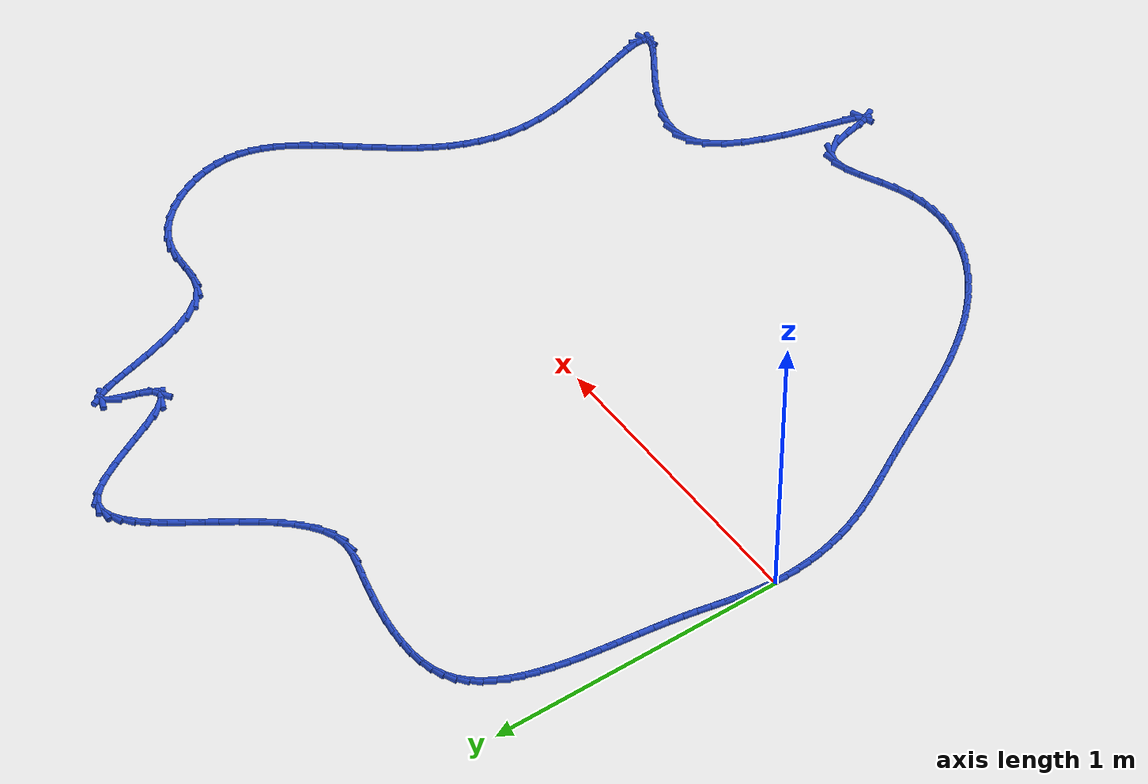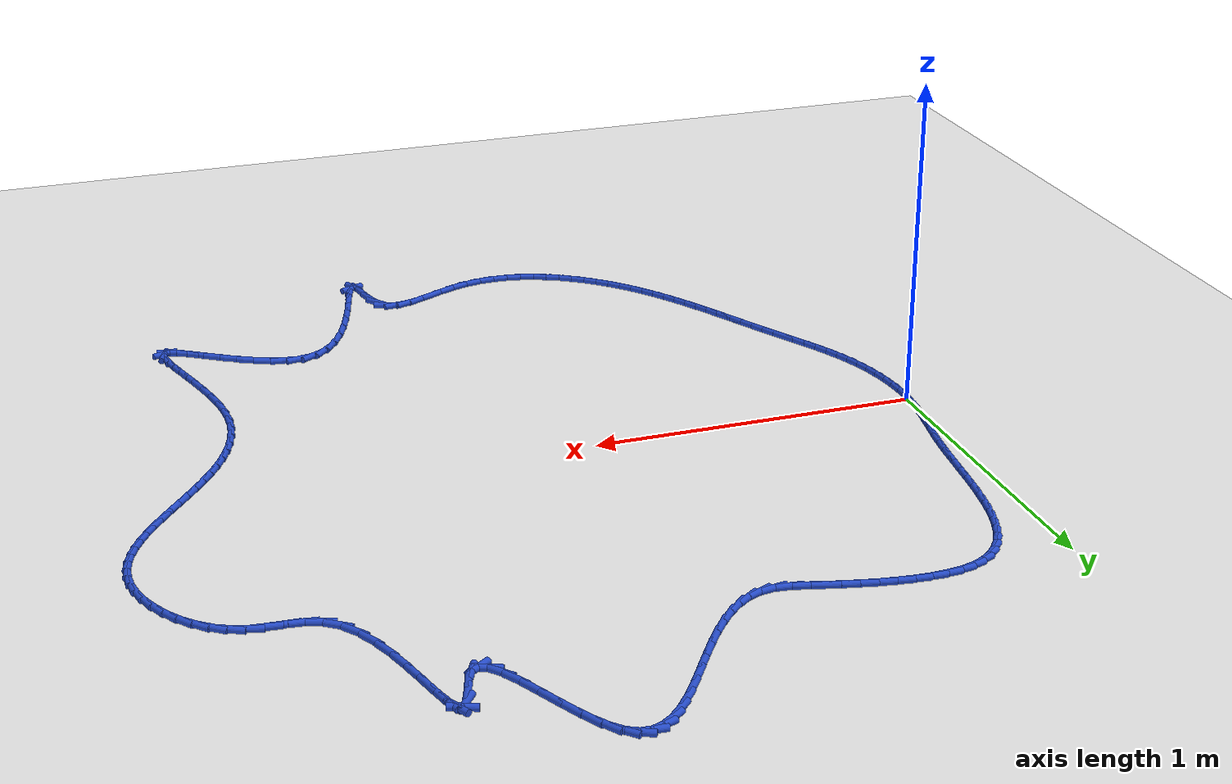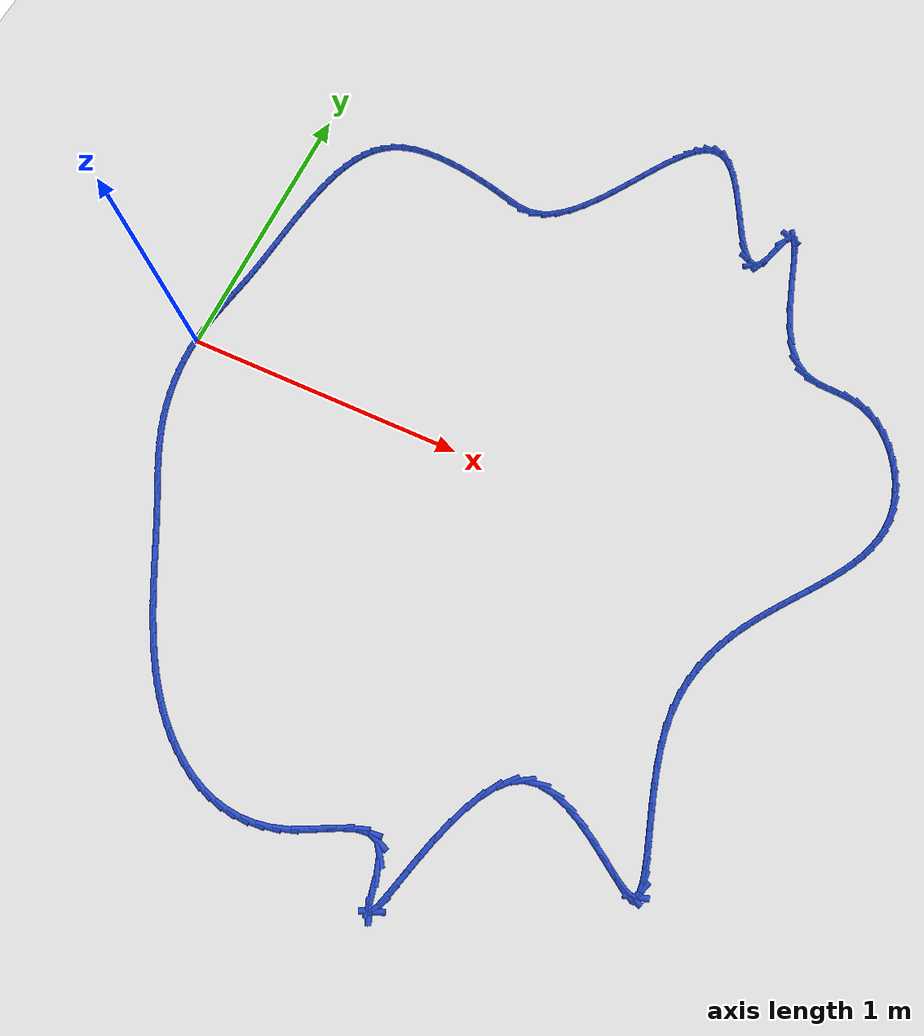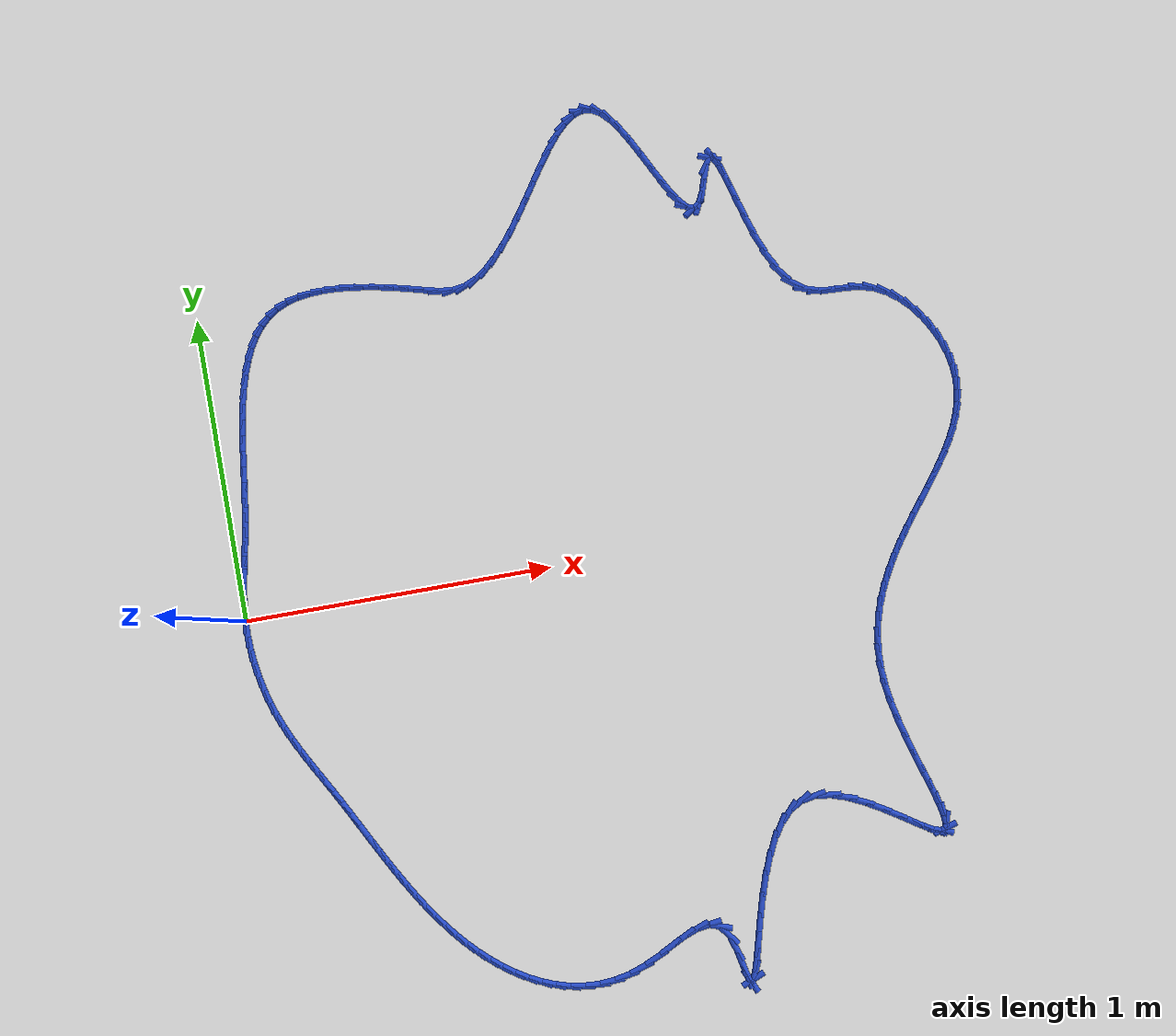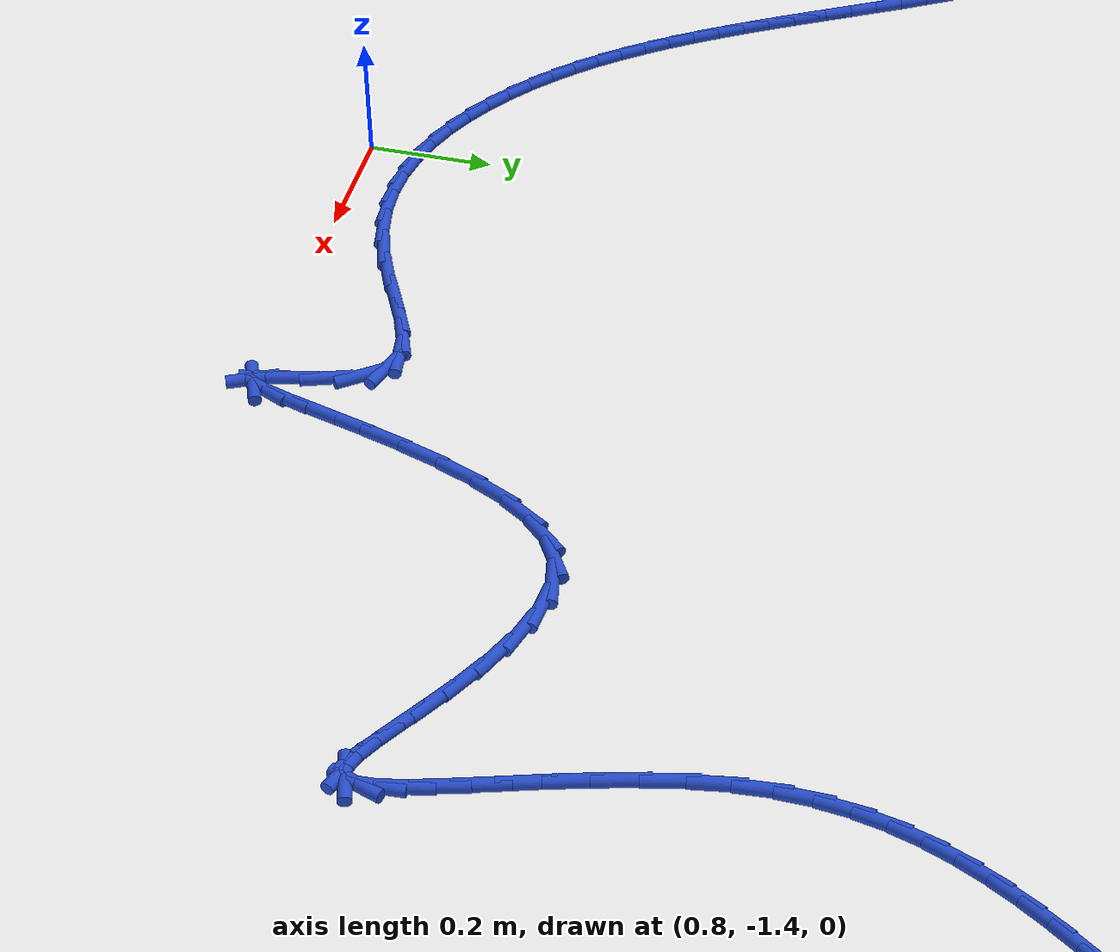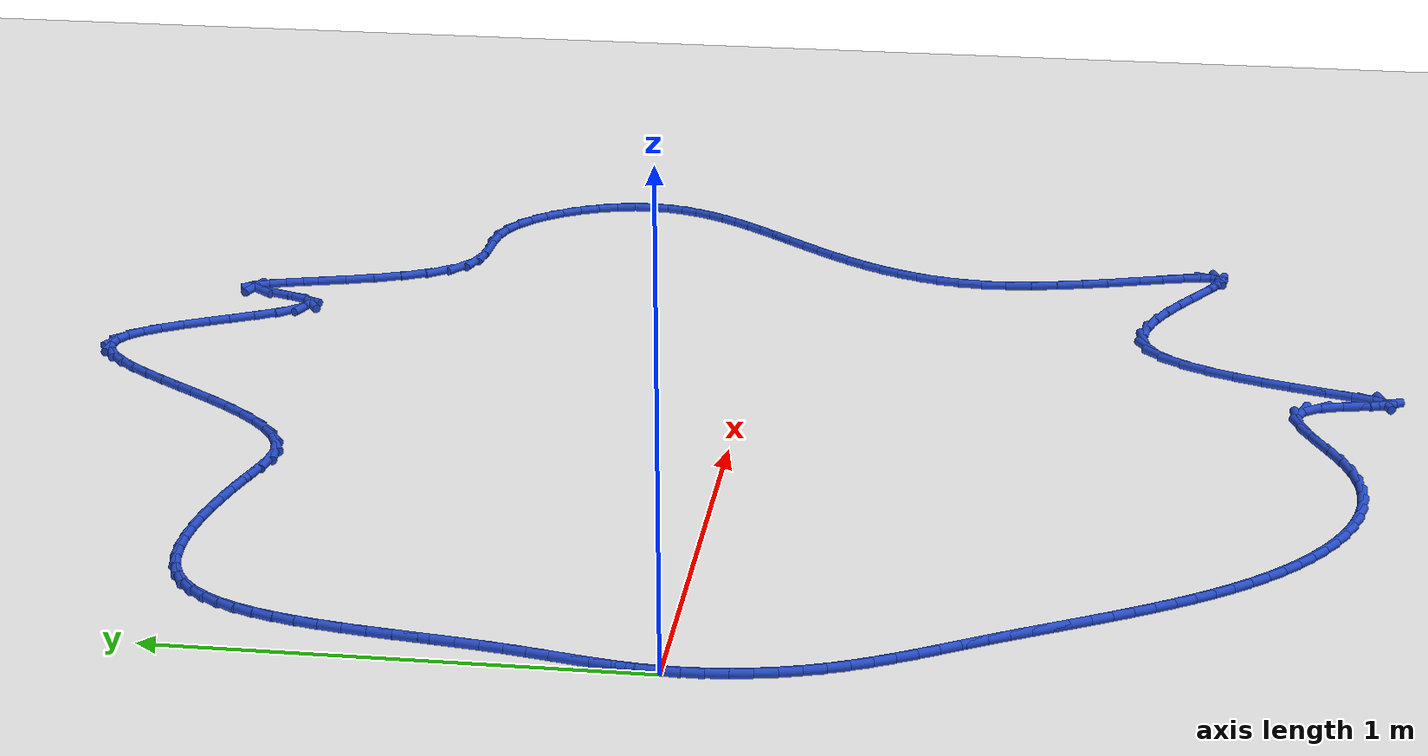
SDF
<sdf version="1.6">
 <world name="default">
  <light name="sun" type="directional">
   <pose>0 0 10 0 -0 0</pose>
   <diffuse>0.8 0.8 0.8 1</diffuse>
   <specular>0.2 0.2 0.2 1</specular>
   <attenuation>
    <range>1000</range>
    <constant>0.9</constant>
    <linear>0.01</linear>
    <quadratic>0.001</quadratic>
   </attenuation>
   <direction>-0.5 0.1 -0.9</direction>
  </light>
  <model name="ground_plane">
   <static>1</static>
   <link name="link">
    <collision name="collision">
     <geometry><plane><normal>0 0 1</normal><size>100 100</size></plane></geometry>
     <surface><friction><ode><mu>100</mu><mu2>50</mu2></ode></friction></surface>
    </collision>
    <visual name="visual">
     <cast_shadows>0</cast_shadows>
     <geometry><plane><normal>0 0 1</normal><size>100 100</size></plane></geometry>
     <material>
      <script><uri>file://media/materials/scripts/gazebo.material</uri><name>Gazebo/WhiteGlow</name></script>
     </material>
    </visual>
   </link>
  </model>
  <gravity>0 0 -9.8</gravity>
  <magnetic_field>6e-06 2.3e-05 -4.2e-05</magnetic_field>
  <atmosphere type="adiabatic"/>
  <physics name="default_physics" default="0" type="ode">
   <max_step_size>0.001</max_step_size>
   <real_time_factor>1</real_time_factor>
   <real_time_update_rate>1000</real_time_update_rate>
  </physics>
  <scene><ambient>0.4 0.4 0.4 1</ambient><background>0.7 0.7 0.7 1</background><shadows>1</shadows></scene>
  <spherical_coordinates>
   <surface_model>EARTH_WGS84</surface_model>
   <latitude_deg>0</latitude_deg>
   <longitude_deg>0</longitude_deg>
   <elevation>0</elevation>
   <heading_deg>0</heading_deg>
  </spherical_coordinates>
  <model name="line">
   <link name="link_0">
    <pose>1.734723475976807e-18 -4.85722573273506e-17 0.01 0 1.57 1.4982520600714382</pose>
    <collision name="collision">
     <geometry><cylinder><radius>0.01</radius><length>0.08</length></cylinder></geometry>
    </collision>
    <visual name="visual">
     <material>
      <script><name>Gazebo/Blue</name><uri>file://media/materials/scripts/gazebo.material</uri></script>
     </material>
     <geometry><cylinder><radius>0.01</radius><length>0.08</length></cylinder></geometry>
    </visual>
   </link>
   <link name="link_1">
    <pose>0.0031635418248118262 0.04353190761836666 0.01 0 1.57 1.4481290351159648</pose>
    <collision name="collision">
     <geometry><cylinder><radius>0.01</radius><length>0.08</length></cylinder></geometry>
    </collision>
    <visual name="visual">
     <material>
      <script><name>Gazebo/Blue</name><uri>file://media/materials/scripts/gazebo.material</uri></script>
     </material>
     <geometry><cylinder><radius>0.01</radius><length>0.08</length></cylinder></geometry>
    </visual>
   </link>
   <link name="link_2">
    <pose>0.008481299447627183 0.08666531495928027 0.01 0 1.57 1.4110172237927368</pose>
    <collision name="collision">
     <geometry><cylinder><radius>0.01</radius><length>0.08</length></cylinder></geometry>
    </collision>
    <visual name="visual">
     <material>
      <script><name>Gazebo/Blue</name><uri>file://media/materials/scripts/gazebo.material</uri></script>
     </material>
     <geometry><cylinder><radius>0.01</radius><length>0.08</length></cylinder></geometry>
    </visual>
   </link>
   <link name="link_3">
    <pose>0.015428172090924824 0.12977267535093684 0.01 0 1.57 1.3875988910370318</pose>
    <collision name="collision">
     <geometry><cylinder><radius>0.01</radius><length>0.08</length></cylinder></geometry>
    </collision>
    <visual name="visual">
     <material>
      <script><name>Gazebo/Blue</name><uri>file://media/materials/scripts/gazebo.material</uri></script>
     </material>
     <geometry><cylinder><radius>0.01</radius><length>0.08</length></cylinder></geometry>
    </visual>
   </link>
   <link name="link_4">
    <pose>0.023479058977183512 0.17322644212153263 0.01 0 1.57 1.3778611131472942</pose>
    <collision name="collision">
     <geometry><cylinder><radius>0.01</radius><length>0.08</length></cylinder></geometry>
    </collision>
    <visual name="visual">
     <material>
      <script><name>Gazebo/Blue</name><uri>file://media/materials/scripts/gazebo.material</uri></script>
     </material>
     <geometry><cylinder><radius>0.01</radius><length>0.08</length></cylinder></geometry>
    </visual>
   </link>
   <link name="link_5">
    <pose>0.03210885932888199 0.2173990685992637 0.01 0 1.57 1.3812552790821984</pose>
    <collision name="collision">
     <geometry><cylinder><radius>0.01</radius><length>0.08</length></cylinder></geometry>
    </collision>
    <visual name="visual">
     <material>
      <script><name>Gazebo/Blue</name><uri>file://media/materials/scripts/gazebo.material</uri></script>
     </material>
     <geometry><cylinder><radius>0.01</radius><length>0.08</length></cylinder></geometry>
    </visual>
   </link>
   <link name="link_6">
    <pose>0.04079247236849904 0.26266300811232635 0.01 0 1.57 1.3968244775304373</pose>
    <collision name="collision">
     <geometry><cylinder><radius>0.01</radius><length>0.08</length></cylinder></geometry>
    </collision>
    <visual name="visual">
     <material>
      <script><name>Gazebo/Blue</name><uri>file://media/materials/scripts/gazebo.material</uri></script>
     </material>
     <geometry><cylinder><radius>0.01</radius><length>0.08</length></cylinder></geometry>
    </visual>
   </link>
   <link name="link_7">
    <pose>0.04900479738674748 0.3093907139218665 0.01 0 1.57 1.4199535878203715</pose>
    <collision name="collision">
     <geometry><cylinder><radius>0.01</radius><length>0.08</length></cylinder></geometry>
    </collision>
    <visual name="visual">
     <material>
      <script><name>Gazebo/Blue</name><uri>file://media/materials/scripts/gazebo.material</uri></script>
     </material>
     <geometry><cylinder><radius>0.01</radius><length>0.08</length></cylinder></geometry>
    </visual>
   </link>
   <link name="link_8">
    <pose>0.05636485738914827 0.3578130160995567 0.01 0 1.57 1.4372459033091183</pose>
    <collision name="collision">
     <geometry><cylinder><radius>0.01</radius><length>0.08</length></cylinder></geometry>
    </collision>
    <visual name="visual">
     <material>
      <script><name>Gazebo/Blue</name><uri>file://media/materials/scripts/gazebo.material</uri></script>
     </material>
     <geometry><cylinder><radius>0.01</radius><length>0.08</length></cylinder></geometry>
    </visual>
   </link>
   <link name="link_9">
    <pose>0.06305474474149994 0.4076074445276917 0.01 0 1.57 1.446428261008948</pose>
    <collision name="collision">
     <geometry><cylinder><radius>0.01</radius><length>0.08</length></cylinder></geometry>
    </collision>
    <visual name="visual">
     <material>
      <script><name>Gazebo/Blue</name><uri>file://media/materials/scripts/gazebo.material</uri></script>
     </material>
     <geometry><cylinder><radius>0.01</radius><length>0.08</length></cylinder></geometry>
    </visual>
   </link>
   <link name="link_10">
    <pose>0.06939404057874507 0.45831642572942244 0.01 0 1.57 1.4481247192318198</pose>
    <collision name="collision">
     <geometry><cylinder><radius>0.01</radius><length>0.08</length></cylinder></geometry>
    </collision>
    <visual name="visual">
     <material>
      <script><name>Gazebo/Blue</name><uri>file://media/materials/scripts/gazebo.material</uri></script>
     </material>
     <geometry><cylinder><radius>0.01</radius><length>0.08</length></cylinder></geometry>
    </visual>
   </link>
   <link name="link_11">
    <pose>0.07570232603582619 0.509482386227899 0.01 0 1.57 1.4425716549833085</pose>
    <collision name="collision">
     <geometry><cylinder><radius>0.01</radius><length>0.08</length></cylinder></geometry>
    </collision>
    <visual name="visual">
     <material>
      <script><name>Gazebo/Blue</name><uri>file://media/materials/scripts/gazebo.material</uri></script>
     </material>
     <geometry><cylinder><radius>0.01</radius><length>0.08</length></cylinder></geometry>
    </visual>
   </link>
   <link name="link_12">
    <pose>0.08229918224768584 0.5606477525462722 0.01 0 1.57 1.4296507228113342</pose>
    <collision name="collision">
     <geometry><cylinder><radius>0.01</radius><length>0.08</length></cylinder></geometry>
    </collision>
    <visual name="visual">
     <material>
      <script><name>Gazebo/Blue</name><uri>file://media/materials/scripts/gazebo.material</uri></script>
     </material>
     <geometry><cylinder><radius>0.01</radius><length>0.08</length></cylinder></geometry>
    </visual>
   </link>
   <link name="link_13">
    <pose>0.08950419034926657 0.6113549512076925 0.01 0 1.57 1.4088899671083515</pose>
    <collision name="collision">
     <geometry><cylinder><radius>0.01</radius><length>0.08</length></cylinder></geometry>
    </collision>
    <visual name="visual">
     <material>
      <script><name>Gazebo/Blue</name><uri>file://media/materials/scripts/gazebo.material</uri></script>
     </material>
     <geometry><cylinder><radius>0.01</radius><length>0.08</length></cylinder></geometry>
    </visual>
   </link>
   <link name="link_14">
    <pose>0.09763693147551093 0.6611464087353103 0.01 0 1.57 1.3794366495867223</pose>
    <collision name="collision">
     <geometry><cylinder><radius>0.01</radius><length>0.08</length></cylinder></geometry>
    </collision>
    <visual name="visual">
     <material>
      <script><name>Gazebo/Blue</name><uri>file://media/materials/scripts/gazebo.material</uri></script>
     </material>
     <geometry><cylinder><radius>0.01</radius><length>0.08</length></cylinder></geometry>
    </visual>
   </link>
   <link name="link_15">
    <pose>0.10701698676136147 0.7095645516522763 0.01 0 1.57 1.3400058128744678</pose>
    <collision name="collision">
     <geometry><cylinder><radius>0.01</radius><length>0.08</length></cylinder></geometry>
    </collision>
    <visual name="visual">
     <material>
      <script><name>Gazebo/Blue</name><uri>file://media/materials/scripts/gazebo.material</uri></script>
     </material>
     <geometry><cylinder><radius>0.01</radius><length>0.08</length></cylinder></geometry>
    </visual>
   </link>
   <link name="link_16">
    <pose>0.11796393734176075 0.7561518064817413 0.01 0 1.57 1.288814267215109</pose>
    <collision name="collision">
     <geometry><cylinder><radius>0.01</radius><length>0.08</length></cylinder></geometry>
    </collision>
    <visual name="visual">
     <material>
      <script><name>Gazebo/Blue</name><uri>file://media/materials/scripts/gazebo.material</uri></script>
     </material>
     <geometry><cylinder><radius>0.01</radius><length>0.08</length></cylinder></geometry>
    </visual>
   </link>
   <link name="link_17">
    <pose>0.13079736435165132 0.8004505997468553 0.01 0 1.57 1.2235269560680018</pose>
    <collision name="collision">
     <geometry><cylinder><radius>0.01</radius><length>0.08</length></cylinder></geometry>
    </collision>
    <visual name="visual">
     <material>
      <script><name>Gazebo/Blue</name><uri>file://media/materials/scripts/gazebo.material</uri></script>
     </material>
     <geometry><cylinder><radius>0.01</radius><length>0.08</length></cylinder></geometry>
    </visual>
   </link>
   <link name="link_18">
    <pose>0.1458368489259757 0.8420033579707691 0.01 0 1.57 1.1412834094080753</pose>
    <collision name="collision">
     <geometry><cylinder><radius>0.01</radius><length>0.08</length></cylinder></geometry>
    </collision>
    <visual name="visual">
     <material>
      <script><name>Gazebo/Blue</name><uri>file://media/materials/scripts/gazebo.material</uri></script>
     </material>
     <geometry><cylinder><radius>0.01</radius><length>0.08</length></cylinder></geometry>
    </visual>
   </link>
   <link name="link_19">
    <pose>0.16340197219967645 0.8803525076766332 0.01 0 1.57 1.038951125923565</pose>
    <collision name="collision">
     <geometry><cylinder><radius>0.01</radius><length>0.08</length></cylinder></geometry>
    </collision>
    <visual name="visual">
     <material>
      <script><name>Gazebo/Blue</name><uri>file://media/materials/scripts/gazebo.material</uri></script>
     </material>
     <geometry><cylinder><radius>0.01</radius><length>0.08</length></cylinder></geometry>
    </visual>
   </link>
   <link name="link_20">
    <pose>0.18381231530769612 0.915040475387598 0.01 0 1.57 0.9138612648375493</pose>
    <collision name="collision">
     <geometry><cylinder><radius>0.01</radius><length>0.08</length></cylinder></geometry>
    </collision>
    <visual name="visual">
     <material>
      <script><name>Gazebo/Blue</name><uri>file://media/materials/scripts/gazebo.material</uri></script>
     </material>
     <geometry><cylinder><radius>0.01</radius><length>0.08</length></cylinder></geometry>
    </visual>
   </link>
   <link name="link_21">
    <pose>0.2073874593849773 0.9456096876268147 0.01 0 1.57 0.765295415689402</pose>
    <collision name="collision">
     <geometry><cylinder><radius>0.01</radius><length>0.08</length></cylinder></geometry>
    </collision>
    <visual name="visual">
     <material>
      <script><name>Gazebo/Blue</name><uri>file://media/materials/scripts/gazebo.material</uri></script>
     </material>
     <geometry><cylinder><radius>0.01</radius><length>0.08</length></cylinder></geometry>
    </visual>
   </link>
   <link name="link_22">
    <pose>0.23444698556646254 0.9716025709174333 0.01 0 1.57 0.5965517758028859</pose>
    <collision name="collision">
     <geometry><cylinder><radius>0.01</radius><length>0.08</length></cylinder></geometry>
    </collision>
    <visual name="visual">
     <material>
      <script><name>Gazebo/Blue</name><uri>file://media/materials/scripts/gazebo.material</uri></script>
     </material>
     <geometry><cylinder><radius>0.01</radius><length>0.08</length></cylinder></geometry>
    </visual>
   </link>
   <link name="link_23">
    <pose>0.26531047498709426 0.9925615517826041 0.01 0 1.57 0.42097119625308793</pose>
    <collision name="collision">
     <geometry><cylinder><radius>0.01</radius><length>0.08</length></cylinder></geometry>
    </collision>
    <visual name="visual">
     <material>
      <script><name>Gazebo/Blue</name><uri>file://media/materials/scripts/gazebo.material</uri></script>
     </material>
     <geometry><cylinder><radius>0.01</radius><length>0.08</length></cylinder></geometry>
    </visual>
   </link>
   <link name="link_24">
    <pose>0.3001694410182661 1.0081692331149341 0.01 0 1.57 0.26814940204424326</pose>
    <collision name="collision">
     <geometry><cylinder><radius>0.01</radius><length>0.08</length></cylinder></geometry>
    </collision>
    <visual name="visual">
     <material>
      <script><name>Gazebo/Blue</name><uri>file://media/materials/scripts/gazebo.material</uri></script>
     </material>
     <geometry><cylinder><radius>0.01</radius><length>0.08</length></cylinder></geometry>
    </visual>
   </link>
   <link name="link_25">
    <pose>0.33863879639280187 1.0187393351304022 0.01 0 1.57 0.14403356371412587</pose>
    <collision name="collision">
     <geometry><cylinder><radius>0.01</radius><length>0.08</length></cylinder></geometry>
    </collision>
    <visual name="visual">
     <material>
      <script><name>Gazebo/Blue</name><uri>file://media/materials/scripts/gazebo.material</uri></script>
     </material>
     <geometry><cylinder><radius>0.01</radius><length>0.08</length></cylinder></geometry>
    </visual>
   </link>
   <link name="link_26">
    <pose>0.3801712516646629 1.0247631161851134 0.01 0 1.57 0.04466507645924687</pose>
    <collision name="collision">
     <geometry><cylinder><radius>0.01</radius><length>0.08</length></cylinder></geometry>
    </collision>
    <visual name="visual">
     <material>
      <script><name>Gazebo/Blue</name><uri>file://media/materials/scripts/gazebo.material</uri></script>
     </material>
     <geometry><cylinder><radius>0.01</radius><length>0.08</length></cylinder></geometry>
    </visual>
   </link>
   <link name="link_27">
    <pose>0.4242195085532895 1.0267318443049847 0.01 0 1.57 -0.034648645979585904</pose>
    <collision name="collision">
     <geometry><cylinder><radius>0.01</radius><length>0.08</length></cylinder></geometry>
    </collision>
    <visual name="visual">
     <material>
      <script><name>Gazebo/Blue</name><uri>file://media/materials/scripts/gazebo.material</uri></script>
     </material>
     <geometry><cylinder><radius>0.01</radius><length>0.08</length></cylinder></geometry>
    </visual>
   </link>
   <link name="link_28">
    <pose>0.470236268778122 1.0251367875159334 0.01 0 1.57 -0.09807751935325891</pose>
    <collision name="collision">
     <geometry><cylinder><radius>0.01</radius><length>0.08</length></cylinder></geometry>
    </collision>
    <visual name="visual">
     <material>
      <script><name>Gazebo/Blue</name><uri>file://media/materials/scripts/gazebo.material</uri></script>
     </material>
     <geometry><cylinder><radius>0.01</radius><length>0.08</length></cylinder></geometry>
    </visual>
   </link>
   <link name="link_29">
    <pose>0.5176742340586009 1.020469213843877 0.01 0 1.57 -0.1489312786633972</pose>
    <collision name="collision">
     <geometry><cylinder><radius>0.01</radius><length>0.08</length></cylinder></geometry>
    </collision>
    <visual name="visual">
     <material>
      <script><name>Gazebo/Blue</name><uri>file://media/materials/scripts/gazebo.material</uri></script>
     </material>
     <geometry><cylinder><radius>0.01</radius><length>0.08</length></cylinder></geometry>
    </visual>
   </link>
   <link name="link_30">
    <pose>0.5659861061141667 1.0132203913147317 0.01 0 1.57 -0.18969581710606048</pose>
    <collision name="collision">
     <geometry><cylinder><radius>0.01</radius><length>0.08</length></cylinder></geometry>
    </collision>
    <visual name="visual">
     <material>
      <script><name>Gazebo/Blue</name><uri>file://media/materials/scripts/gazebo.material</uri></script>
     </material>
     <geometry><cylinder><radius>0.01</radius><length>0.08</length></cylinder></geometry>
    </visual>
   </link>
   <link name="link_31">
    <pose>0.6146245866642596 1.003881587954415 0.01 0 1.57 -0.22216967657675998</pose>
    <collision name="collision">
     <geometry><cylinder><radius>0.01</radius><length>0.08</length></cylinder></geometry>
    </collision>
    <visual name="visual">
     <material>
      <script><name>Gazebo/Blue</name><uri>file://media/materials/scripts/gazebo.material</uri></script>
     </material>
     <geometry><cylinder><radius>0.01</radius><length>0.08</length></cylinder></geometry>
    </visual>
   </link>
   <link name="link_32">
    <pose>0.6630423774283201 0.9929440717888439 0.01 0 1.57 -0.24759428176950896</pose>
    <collision name="collision">
     <geometry><cylinder><radius>0.01</radius><length>0.08</length></cylinder></geometry>
    </collision>
    <visual name="visual">
     <material>
      <script><name>Gazebo/Blue</name><uri>file://media/materials/scripts/gazebo.material</uri></script>
     </material>
     <geometry><cylinder><radius>0.01</radius><length>0.08</length></cylinder></geometry>
    </visual>
   </link>
   <link name="link_33">
    <pose>0.7106921801257884 0.9808991108439356 0.01 0 1.57 -0.2659017500576483</pose>
    <collision name="collision">
     <geometry><cylinder><radius>0.01</radius><length>0.08</length></cylinder></geometry>
    </collision>
    <visual name="visual">
     <material>
      <script><name>Gazebo/Blue</name><uri>file://media/materials/scripts/gazebo.material</uri></script>
     </material>
     <geometry><cylinder><radius>0.01</radius><length>0.08</length></cylinder></geometry>
    </visual>
   </link>
   <link name="link_34">
    <pose>0.7570323707288211 0.9682783157123244 0.01 0 1.57 -0.2380853753194528</pose>
    <collision name="collision">
     <geometry><cylinder><radius>0.01</radius><length>0.08</length></cylinder></geometry>
    </collision>
    <visual name="visual">
     <material>
      <script><name>Gazebo/Blue</name><uri>file://media/materials/scripts/gazebo.material</uri></script>
     </material>
     <geometry><cylinder><radius>0.01</radius><length>0.08</length></cylinder></geometry>
    </visual>
   </link>
   <link name="link_35">
    <pose>0.8017753994072406 0.957419703183818 0.01 0 1.57 -0.09836362308103652</pose>
    <collision name="collision">
     <geometry><cylinder><radius>0.01</radius><length>0.08</length></cylinder></geometry>
    </collision>
    <visual name="visual">
     <material>
      <script><name>Gazebo/Blue</name><uri>file://media/materials/scripts/gazebo.material</uri></script>
     </material>
     <geometry><cylinder><radius>0.01</radius><length>0.08</length></cylinder></geometry>
    </visual>
   </link>
   <link name="link_36">
    <pose>0.8449845640259951 0.9531557324456068 0.01 0 1.57 0.16148460717505797</pose>
    <collision name="collision">
     <geometry><cylinder><radius>0.01</radius><length>0.08</length></cylinder></geometry>
    </collision>
    <visual name="visual">
     <material>
      <script><name>Gazebo/Blue</name><uri>file://media/materials/scripts/gazebo.material</uri></script>
     </material>
     <geometry><cylinder><radius>0.01</radius><length>0.08</length></cylinder></geometry>
    </visual>
   </link>
   <link name="link_37">
    <pose>0.8867484457921553 0.9599591981775714 0.01 0 1.57 0.4220266790031647</pose>
    <collision name="collision">
     <geometry><cylinder><radius>0.01</radius><length>0.08</length></cylinder></geometry>
    </collision>
    <visual name="visual">
     <material>
      <script><name>Gazebo/Blue</name><uri>file://media/materials/scripts/gazebo.material</uri></script>
     </material>
     <geometry><cylinder><radius>0.01</radius><length>0.08</length></cylinder></geometry>
    </visual>
   </link>
   <link name="link_38">
    <pose>0.9271526825461279 0.9781009269569306 0.01 0 1.57 0.6175205332455116</pose>
    <collision name="collision">
     <geometry><cylinder><radius>0.01</radius><length>0.08</length></cylinder></geometry>
    </collision>
    <visual name="visual">
     <material>
      <script><name>Gazebo/Blue</name><uri>file://media/materials/scripts/gazebo.material</uri></script>
     </material>
     <geometry><cylinder><radius>0.01</radius><length>0.08</length></cylinder></geometry>
    </visual>
   </link>
   <link name="link_39">
    <pose>0.966281537390652 1.0058891615231023 0.01 0 1.57 0.7554648651735559</pose>
    <collision name="collision">
     <geometry><cylinder><radius>0.01</radius><length>0.08</length></cylinder></geometry>
    </collision>
    <visual name="visual">
     <material>
      <script><name>Gazebo/Blue</name><uri>file://media/materials/scripts/gazebo.material</uri></script>
     </material>
     <geometry><cylinder><radius>0.01</radius><length>0.08</length></cylinder></geometry>
    </visual>
   </link>
   <link name="link_40">
    <pose>1.0042192656612905 1.041621056151405 0.01 0 1.57 0.8505547769216781</pose>
    <collision name="collision">
     <geometry><cylinder><radius>0.01</radius><length>0.08</length></cylinder></geometry>
    </collision>
    <visual name="visual">
     <material>
      <script><name>Gazebo/Blue</name><uri>file://media/materials/scripts/gazebo.material</uri></script>
     </material>
     <geometry><cylinder><radius>0.01</radius><length>0.08</length></cylinder></geometry>
    </visual>
   </link>
   <link name="link_41">
    <pose>1.0410501226936089 1.0835937651171585 0.01 0 1.57 0.9146848388607492</pose>
    <collision name="collision">
     <geometry><cylinder><radius>0.01</radius><length>0.08</length></cylinder></geometry>
    </collision>
    <visual name="visual">
     <material>
      <script><name>Gazebo/Blue</name><uri>file://media/materials/scripts/gazebo.material</uri></script>
     </material>
     <geometry><cylinder><radius>0.01</radius><length>0.08</length></cylinder></geometry>
    </visual>
   </link>
   <link name="link_42">
    <pose>1.0768583638231708 1.1301044426956826 0.01 0 1.57 0.9556256558031722</pose>
    <collision name="collision">
     <geometry><cylinder><radius>0.01</radius><length>0.08</length></cylinder></geometry>
    </collision>
    <visual name="visual">
     <material>
      <script><name>Gazebo/Blue</name><uri>file://media/materials/scripts/gazebo.material</uri></script>
     </material>
     <geometry><cylinder><radius>0.01</radius><length>0.08</length></cylinder></geometry>
    </visual>
   </link>
   <link name="link_43">
    <pose>1.1117282443855405 1.1794502431622962 0.01 0 1.57 0.9778218241050537</pose>
    <collision name="collision">
     <geometry><cylinder><radius>0.01</radius><length>0.08</length></cylinder></geometry>
    </collision>
    <visual name="visual">
     <material>
      <script><name>Gazebo/Blue</name><uri>file://media/materials/scripts/gazebo.material</uri></script>
     </material>
     <geometry><cylinder><radius>0.01</radius><length>0.08</length></cylinder></geometry>
    </visual>
   </link>
   <link name="link_44">
    <pose>1.1457440197162827 1.229928320792319 0.01 0 1.57 0.9831509697490062</pose>
    <collision name="collision">
     <geometry><cylinder><radius>0.01</radius><length>0.08</length></cylinder></geometry>
    </collision>
    <visual name="visual">
     <material>
      <script><name>Gazebo/Blue</name><uri>file://media/materials/scripts/gazebo.material</uri></script>
     </material>
     <geometry><cylinder><radius>0.01</radius><length>0.08</length></cylinder></geometry>
    </visual>
   </link>
   <link name="link_45">
    <pose>1.1789899451509618 1.2798358298610706 0.01 0 1.57 0.9711955081836428</pose>
    <collision name="collision">
     <geometry><cylinder><radius>0.01</radius><length>0.08</length></cylinder></geometry>
    </collision>
    <visual name="visual">
     <material>
      <script><name>Gazebo/Blue</name><uri>file://media/materials/scripts/gazebo.material</uri></script>
     </material>
     <geometry><cylinder><radius>0.01</radius><length>0.08</length></cylinder></geometry>
    </visual>
   </link>
   <link name="link_46">
    <pose>1.211550276025141 1.32746992464387 0.01 0 1.57 0.9388933718151196</pose>
    <collision name="collision">
     <geometry><cylinder><radius>0.01</radius><length>0.08</length></cylinder></geometry>
    </collision>
    <visual name="visual">
     <material>
      <script><name>Gazebo/Blue</name><uri>file://media/materials/scripts/gazebo.material</uri></script>
     </material>
     <geometry><cylinder><radius>0.01</radius><length>0.08</length></cylinder></geometry>
    </visual>
   </link>
   <link name="link_47">
    <pose>1.2435092676743862 1.3711277594160374 0.01 0 1.57 0.879283843018872</pose>
    <collision name="collision">
     <geometry><cylinder><radius>0.01</radius><length>0.08</length></cylinder></geometry>
    </collision>
    <visual name="visual">
     <material>
      <script><name>Gazebo/Blue</name><uri>file://media/materials/scripts/gazebo.material</uri></script>
     </material>
     <geometry><cylinder><radius>0.01</radius><length>0.08</length></cylinder></geometry>
    </visual>
   </link>
   <link name="link_48">
    <pose>1.27495117543426 1.4091064884528917 0.01 0 1.57 0.7787056913636458</pose>
    <collision name="collision">
     <geometry><cylinder><radius>0.01</radius><length>0.08</length></cylinder></geometry>
    </collision>
    <visual name="visual">
     <material>
      <script><name>Gazebo/Blue</name><uri>file://media/materials/scripts/gazebo.material</uri></script>
     </material>
     <geometry><cylinder><radius>0.01</radius><length>0.08</length></cylinder></geometry>
    </visual>
   </link>
   <link name="link_49">
    <pose>1.305960254640328 1.4397032660297522 0.01 0 1.57 0.6118114277231279</pose>
    <collision name="collision">
     <geometry><cylinder><radius>0.01</radius><length>0.08</length></cylinder></geometry>
    </collision>
    <visual name="visual">
     <material>
      <script><name>Gazebo/Blue</name><uri>file://media/materials/scripts/gazebo.material</uri></script>
     </material>
     <geometry><cylinder><radius>0.01</radius><length>0.08</length></cylinder></geometry>
    </visual>
   </link>
   <link name="link_50">
    <pose>1.3366207606281537 1.4612152464219388 0.01 0 1.57 0.3391835222651856</pose>
    <collision name="collision">
     <geometry><cylinder><radius>0.01</radius><length>0.08</length></cylinder></geometry>
    </collision>
    <visual name="visual">
     <material>
      <script><name>Gazebo/Blue</name><uri>file://media/materials/scripts/gazebo.material</uri></script>
     </material>
     <geometry><cylinder><radius>0.01</radius><length>0.08</length></cylinder></geometry>
    </visual>
   </link>
   <link name="link_51">
    <pose>1.3670169487333024 1.4719395839047713 0.01 0 1.57 -0.05838418707897125</pose>
    <collision name="collision">
     <geometry><cylinder><radius>0.01</radius><length>0.08</length></cylinder></geometry>
    </collision>
    <visual name="visual">
     <material>
      <script><name>Gazebo/Blue</name><uri>file://media/materials/scripts/gazebo.material</uri></script>
     </material>
     <geometry><cylinder><radius>0.01</radius><length>0.08</length></cylinder></geometry>
    </visual>
   </link>
   <link name="link_52">
    <pose>1.397233074291337 1.470173432753568 0.01 0 1.57 -0.4872475545735973</pose>
    <collision name="collision">
     <geometry><cylinder><radius>0.01</radius><length>0.08</length></cylinder></geometry>
    </collision>
    <visual name="visual">
     <material>
      <script><name>Gazebo/Blue</name><uri>file://media/materials/scripts/gazebo.material</uri></script>
     </material>
     <geometry><cylinder><radius>0.01</radius><length>0.08</length></cylinder></geometry>
    </visual>
   </link>
   <link name="link_53">
    <pose>1.4273533926378228 1.4542139472436493 0.01 0 1.57 -0.8073012380683111</pose>
    <collision name="collision">
     <geometry><cylinder><radius>0.01</radius><length>0.08</length></cylinder></geometry>
    </collision>
    <visual name="visual">
     <material>
      <script><name>Gazebo/Blue</name><uri>file://media/materials/scripts/gazebo.material</uri></script>
     </material>
     <geometry><cylinder><radius>0.01</radius><length>0.08</length></cylinder></geometry>
    </visual>
   </link>
   <link name="link_54">
    <pose>1.4574407283180275 1.4227788659387977 0.01 0 1.57 -0.9779283759990263</pose>
    <collision name="collision">
     <geometry><cylinder><radius>0.01</radius><length>0.08</length></cylinder></geometry>
    </collision>
    <visual name="visual">
     <material>
      <script><name>Gazebo/Blue</name><uri>file://media/materials/scripts/gazebo.material</uri></script>
     </material>
     <geometry><cylinder><radius>0.01</radius><length>0.08</length></cylinder></geometry>
    </visual>
   </link>
   <link name="link_55">
    <pose>1.487365526032299 1.3783614270027067 0.01 0 1.57 -1.0617486226155675</pose>
    <collision name="collision">
     <geometry><cylinder><radius>0.01</radius><length>0.08</length></cylinder></geometry>
    </collision>
    <visual name="visual">
     <material>
      <script><name>Gazebo/Blue</name><uri>file://media/materials/scripts/gazebo.material</uri></script>
     </material>
     <geometry><cylinder><radius>0.01</radius><length>0.08</length></cylinder></geometry>
    </visual>
   </link>
   <link name="link_56">
    <pose>1.5168966385264455 1.3254486345462557 0.01 0 1.57 -1.1007890962793665</pose>
    <collision name="collision">
     <geometry><cylinder><radius>0.01</radius><length>0.08</length></cylinder></geometry>
    </collision>
    <visual name="visual">
     <material>
      <script><name>Gazebo/Blue</name><uri>file://media/materials/scripts/gazebo.material</uri></script>
     </material>
     <geometry><cylinder><radius>0.01</radius><length>0.08</length></cylinder></geometry>
    </visual>
   </link>
   <link name="link_57">
    <pose>1.5458020002137172 1.2685455151722245 0.01 0 1.57 -1.1092316573219194</pose>
    <collision name="collision">
     <geometry><cylinder><radius>0.01</radius><length>0.08</length></cylinder></geometry>
    </collision>
    <visual name="visual">
     <material>
      <script><name>Gazebo/Blue</name><uri>file://media/materials/scripts/gazebo.material</uri></script>
     </material>
     <geometry><cylinder><radius>0.01</radius><length>0.08</length></cylinder></geometry>
    </visual>
   </link>
   <link name="link_58">
    <pose>1.5738495455073662 1.212157095483396 0.01 0 1.57 -1.0875156939405088</pose>
    <collision name="collision">
     <geometry><cylinder><radius>0.01</radius><length>0.08</length></cylinder></geometry>
    </collision>
    <visual name="visual">
     <material>
      <script><name>Gazebo/Blue</name><uri>file://media/materials/scripts/gazebo.material</uri></script>
     </material>
     <geometry><cylinder><radius>0.01</radius><length>0.08</length></cylinder></geometry>
    </visual>
   </link>
   <link name="link_59">
    <pose>1.6008072088206433 1.16078840208255 0.01 0 1.57 -1.021126797336684</pose>
    <collision name="collision">
     <geometry><cylinder><radius>0.01</radius><length>0.08</length></cylinder></geometry>
    </collision>
    <visual name="visual">
     <material>
      <script><name>Gazebo/Blue</name><uri>file://media/materials/scripts/gazebo.material</uri></script>
     </material>
     <geometry><cylinder><radius>0.01</radius><length>0.08</length></cylinder></geometry>
    </visual>
   </link>
   <link name="link_60">
    <pose>1.6264429245668002 1.1189444615724684 0.01 0 1.57 -0.8571966138022475</pose>
    <collision name="collision">
     <geometry><cylinder><radius>0.01</radius><length>0.08</length></cylinder></geometry>
    </collision>
    <visual name="visual">
     <material>
      <script><name>Gazebo/Blue</name><uri>file://media/materials/scripts/gazebo.material</uri></script>
     </material>
     <geometry><cylinder><radius>0.01</radius><length>0.08</length></cylinder></geometry>
    </visual>
   </link>
   <link name="link_61">
    <pose>1.6505246271590883 1.091130300555933 0.01 0 1.57 -0.39439021984326583</pose>
    <collision name="collision">
     <geometry><cylinder><radius>0.01</radius><length>0.08</length></cylinder></geometry>
    </collision>
    <visual name="visual">
     <material>
      <script><name>Gazebo/Blue</name><uri>file://media/materials/scripts/gazebo.material</uri></script>
     </material>
     <geometry><cylinder><radius>0.01</radius><length>0.08</length></cylinder></geometry>
    </visual>
   </link>
   <link name="link_62">
    <pose>1.6728202510107586 1.0818509456357248 0.01 0 1.57 0.5962247881532992</pose>
    <collision name="collision">
     <geometry><cylinder><radius>0.01</radius><length>0.08</length></cylinder></geometry>
    </collision>
    <visual name="visual">
     <material>
      <script><name>Gazebo/Blue</name><uri>file://media/materials/scripts/gazebo.material</uri></script>
     </material>
     <geometry><cylinder><radius>0.01</radius><length>0.08</length></cylinder></geometry>
    </visual>
   </link>
   <link name="link_63">
    <pose>1.6930977305350625 1.095611423414625 0.01 0 1.57 1.1229213173697732</pose>
    <collision name="collision">
     <geometry><cylinder><radius>0.01</radius><length>0.08</length></cylinder></geometry>
    </collision>
    <visual name="visual">
     <material>
      <script><name>Gazebo/Blue</name><uri>file://media/materials/scripts/gazebo.material</uri></script>
     </material>
     <geometry><cylinder><radius>0.01</radius><length>0.08</length></cylinder></geometry>
    </visual>
   </link>
   <link name="link_64">
    <pose>1.7112166948940537 1.1333249379952481 0.01 0 1.57 1.244275173853015</pose>
    <collision name="collision">
     <geometry><cylinder><radius>0.01</radius><length>0.08</length></cylinder></geometry>
    </collision>
    <visual name="visual">
     <material>
      <script><name>Gazebo/Blue</name><uri>file://media/materials/scripts/gazebo.material</uri></script>
     </material>
     <geometry><cylinder><radius>0.01</radius><length>0.08</length></cylinder></geometry>
    </visual>
   </link>
   <link name="link_65">
    <pose>1.7274133615835752 1.1811531567971165 0.01 0 1.57 1.2232059594716094</pose>
    <collision name="collision">
     <geometry><cylinder><radius>0.01</radius><length>0.08</length></cylinder></geometry>
    </collision>
    <visual name="visual">
     <material>
      <script><name>Gazebo/Blue</name><uri>file://media/materials/scripts/gazebo.material</uri></script>
     </material>
     <geometry><cylinder><radius>0.01</radius><length>0.08</length></cylinder></geometry>
    </visual>
   </link>
   <link name="link_66">
    <pose>1.7420206127494138 1.2214712461676438 0.01 0 1.57 0.931476409981154</pose>
    <collision name="collision">
     <geometry><cylinder><radius>0.01</radius><length>0.08</length></cylinder></geometry>
    </collision>
    <visual name="visual">
     <material>
      <script><name>Gazebo/Blue</name><uri>file://media/materials/scripts/gazebo.material</uri></script>
     </material>
     <geometry><cylinder><radius>0.01</radius><length>0.08</length></cylinder></geometry>
    </visual>
   </link>
   <link name="link_67">
    <pose>1.7554037255991188 1.2394717060804001 0.01 0 1.57 -0.37375416897787334</pose>
    <collision name="collision">
     <geometry><cylinder><radius>0.01</radius><length>0.08</length></cylinder></geometry>
    </collision>
    <visual name="visual">
     <material>
      <script><name>Gazebo/Blue</name><uri>file://media/materials/scripts/gazebo.material</uri></script>
     </material>
     <geometry><cylinder><radius>0.01</radius><length>0.08</length></cylinder></geometry>
    </visual>
   </link>
   <link name="link_68">
    <pose>1.7680906688736167 1.2344960338680837 0.01 0 1.57 -1.091372390550766</pose>
    <collision name="collision">
     <geometry><cylinder><radius>0.01</radius><length>0.08</length></cylinder></geometry>
    </collision>
    <visual name="visual">
     <material>
      <script><name>Gazebo/Blue</name><uri>file://media/materials/scripts/gazebo.material</uri></script>
     </material>
     <geometry><cylinder><radius>0.01</radius><length>0.08</length></cylinder></geometry>
    </visual>
   </link>
   <link name="link_69">
    <pose>1.7806603743307834 1.2103178910781083 0.01 0 1.57 -1.2529226455767757</pose>
    <collision name="collision">
     <geometry><cylinder><radius>0.01</radius><length>0.08</length></cylinder></geometry>
    </collision>
    <visual name="visual">
     <material>
      <script><name>Gazebo/Blue</name><uri>file://media/materials/scripts/gazebo.material</uri></script>
     </material>
     <geometry><cylinder><radius>0.01</radius><length>0.08</length></cylinder></geometry>
    </visual>
   </link>
   <link name="link_70">
    <pose>1.7936917914508976 1.1707124805438458 0.01 0 1.57 -1.3028605284781158</pose>
    <collision name="collision">
     <geometry><cylinder><radius>0.01</radius><length>0.08</length></cylinder></geometry>
    </collision>
    <visual name="visual">
     <material>
      <script><name>Gazebo/Blue</name><uri>file://media/materials/scripts/gazebo.material</uri></script>
     </material>
     <geometry><cylinder><radius>0.01</radius><length>0.08</length></cylinder></geometry>
    </visual>
   </link>
   <link name="link_71">
    <pose>1.807763869714237 1.1194550050986676 0.01 0 1.57 -1.311417390988707</pose>
    <collision name="collision">
     <geometry><cylinder><radius>0.01</radius><length>0.08</length></cylinder></geometry>
    </collision>
    <visual name="visual">
     <material>
      <script><name>Gazebo/Blue</name><uri>file://media/materials/scripts/gazebo.material</uri></script>
     </material>
     <geometry><cylinder><radius>0.01</radius><length>0.08</length></cylinder></geometry>
    </visual>
   </link>
   <link name="link_72">
    <pose>1.8234555586010777 1.0603206675759427 0.01 0 1.57 -1.295088983080152</pose>
    <collision name="collision">
     <geometry><cylinder><radius>0.01</radius><length>0.08</length></cylinder></geometry>
    </collision>
    <visual name="visual">
     <material>
      <script><name>Gazebo/Blue</name><uri>file://media/materials/scripts/gazebo.material</uri></script>
     </material>
     <geometry><cylinder><radius>0.01</radius><length>0.08</length></cylinder></geometry>
    </visual>
   </link>
   <link name="link_73">
    <pose>1.8413458075916975 0.9970846708090432 0.01 0 1.57 -1.256422689430696</pose>
    <collision name="collision">
     <geometry><cylinder><radius>0.01</radius><length>0.08</length></cylinder></geometry>
    </collision>
    <visual name="visual">
     <material>
      <script><name>Gazebo/Blue</name><uri>file://media/materials/scripts/gazebo.material</uri></script>
     </material>
     <geometry><cylinder><radius>0.01</radius><length>0.08</length></cylinder></geometry>
    </visual>
   </link>
   <link name="link_74">
    <pose>1.8620135661663737 0.9335222176313391 0.01 0 1.57 -1.1905949414682713</pose>
    <collision name="collision">
     <geometry><cylinder><radius>0.01</radius><length>0.08</length></cylinder></geometry>
    </collision>
    <visual name="visual">
     <material>
      <script><name>Gazebo/Blue</name><uri>file://media/materials/scripts/gazebo.material</uri></script>
     </material>
     <geometry><cylinder><radius>0.01</radius><length>0.08</length></cylinder></geometry>
    </visual>
   </link>
   <link name="link_75">
    <pose>1.8860377838053832 0.8734085108762015 0.01 0 1.57 -1.0845003230859669</pose>
    <collision name="collision">
     <geometry><cylinder><radius>0.01</radius><length>0.08</length></cylinder></geometry>
    </collision>
    <visual name="visual">
     <material>
      <script><name>Gazebo/Blue</name><uri>file://media/materials/scripts/gazebo.material</uri></script>
     </material>
     <geometry><cylinder><radius>0.01</radius><length>0.08</length></cylinder></geometry>
    </visual>
   </link>
   <link name="link_76">
    <pose>1.9139974099890043 0.8205187533770014 0.01 0 1.57 -0.9113555503702386</pose>
    <collision name="collision">
     <geometry><cylinder><radius>0.01</radius><length>0.08</length></cylinder></geometry>
    </collision>
    <visual name="visual">
     <material>
      <script><name>Gazebo/Blue</name><uri>file://media/materials/scripts/gazebo.material</uri></script>
     </material>
     <geometry><cylinder><radius>0.01</radius><length>0.08</length></cylinder></geometry>
    </visual>
   </link>
   <link name="link_77">
    <pose>1.9464713941975127 0.7786281479671091 0.01 0 1.57 -0.6290559682548628</pose>
    <collision name="collision">
     <geometry><cylinder><radius>0.01</radius><length>0.08</length></cylinder></geometry>
    </collision>
    <visual name="visual">
     <material>
      <script><name>Gazebo/Blue</name><uri>file://media/materials/scripts/gazebo.material</uri></script>
     </material>
     <geometry><cylinder><radius>0.01</radius><length>0.08</length></cylinder></geometry>
    </visual>
   </link>
   <link name="link_78">
    <pose>1.9839927782287263 0.7513249685839815 0.01 0 1.57 -0.3117280516410252</pose>
    <collision name="collision">
     <geometry><cylinder><radius>0.01</radius><length>0.08</length></cylinder></geometry>
    </collision>
    <visual name="visual">
     <material>
      <script><name>Gazebo/Blue</name><uri>file://media/materials/scripts/gazebo.material</uri></script>
     </material>
     <geometry><cylinder><radius>0.01</radius><length>0.08</length></cylinder></geometry>
    </visual>
   </link>
   <link name="link_79">
    <pose>2.026011010945434 0.7377852683752131 0.01 0 1.57 -0.112659842152981</pose>
    <collision name="collision">
     <geometry><cylinder><radius>0.01</radius><length>0.08</length></cylinder></geometry>
    </collision>
    <visual name="visual">
     <material>
      <script><name>Gazebo/Blue</name><uri>file://media/materials/scripts/gazebo.material</uri></script>
     </material>
     <geometry><cylinder><radius>0.01</radius><length>0.08</length></cylinder></geometry>
    </visual>
   </link>
   <link name="link_80">
    <pose>2.0708763229668716 0.7327092558884445 0.01 0 1.57 -0.045862318755296644</pose>
    <collision name="collision">
     <geometry><cylinder><radius>0.01</radius><length>0.08</length></cylinder></geometry>
    </collision>
    <visual name="visual">
     <material>
      <script><name>Gazebo/Blue</name><uri>file://media/materials/scripts/gazebo.material</uri></script>
     </material>
     <geometry><cylinder><radius>0.01</radius><length>0.08</length></cylinder></geometry>
    </visual>
   </link>
   <link name="link_81">
    <pose>2.116889911967308 0.73059748519574 0.01 0 1.57 -0.10186053595120187</pose>
    <collision name="collision">
     <geometry><cylinder><radius>0.01</radius><length>0.08</length></cylinder></geometry>
    </collision>
    <visual name="visual">
     <material>
      <script><name>Gazebo/Blue</name><uri>file://media/materials/scripts/gazebo.material</uri></script>
     </material>
     <geometry><cylinder><radius>0.01</radius><length>0.08</length></cylinder></geometry>
    </visual>
   </link>
   <link name="link_82">
    <pose>2.1623529756210096 0.7259505103691627 0.01 0 1.57 -0.27729738008622196</pose>
    <collision name="collision">
     <geometry><cylinder><radius>0.01</radius><length>0.08</length></cylinder></geometry>
    </collision>
    <visual name="visual">
     <material>
      <script><name>Gazebo/Blue</name><uri>file://media/materials/scripts/gazebo.material</uri></script>
     </material>
     <geometry><cylinder><radius>0.01</radius><length>0.08</length></cylinder></geometry>
    </visual>
   </link>
   <link name="link_83">
    <pose>2.2056349764886147 0.7136311329032565 0.01 0 1.57 -0.4833220088425829</pose>
    <collision name="collision">
     <geometry><cylinder><radius>0.01</radius><length>0.08</length></cylinder></geometry>
    </collision>
    <visual name="visual">
     <material>
      <script><name>Gazebo/Blue</name><uri>file://media/materials/scripts/gazebo.material</uri></script>
     </material>
     <geometry><cylinder><radius>0.01</radius><length>0.08</length></cylinder></geometry>
    </visual>
   </link>
   <link name="link_84">
    <pose>2.2458622036798586 0.6925182521907718 0.01 0 1.57 -0.6598079266038612</pose>
    <collision name="collision">
     <geometry><cylinder><radius>0.01</radius><length>0.08</length></cylinder></geometry>
    </collision>
    <visual name="visual">
     <material>
      <script><name>Gazebo/Blue</name><uri>file://media/materials/scripts/gazebo.material</uri></script>
     </material>
     <geometry><cylinder><radius>0.01</radius><length>0.08</length></cylinder></geometry>
    </visual>
   </link>
   <link name="link_85">
    <pose>2.2826323180959727 0.663992100675408 0.01 0 1.57 -0.8091715459402741</pose>
    <collision name="collision">
     <geometry><cylinder><radius>0.01</radius><length>0.08</length></cylinder></geometry>
    </collision>
    <visual name="visual">
     <material>
      <script><name>Gazebo/Blue</name><uri>file://media/materials/scripts/gazebo.material</uri></script>
     </material>
     <geometry><cylinder><radius>0.01</radius><length>0.08</length></cylinder></geometry>
    </visual>
   </link>
   <link name="link_86">
    <pose>2.3155501111633088 0.6294707489118532 0.01 0 1.57 -0.9380800347323993</pose>
    <collision name="collision">
     <geometry><cylinder><radius>0.01</radius><length>0.08</length></cylinder></geometry>
    </collision>
    <visual name="visual">
     <material>
      <script><name>Gazebo/Blue</name><uri>file://media/materials/scripts/gazebo.material</uri></script>
     </material>
     <geometry><cylinder><radius>0.01</radius><length>0.08</length></cylinder></geometry>
    </visual>
   </link>
   <link name="link_87">
    <pose>2.3442203743082217 0.5903722674547941 0.01 0 1.57 -1.0537871378796086</pose>
    <collision name="collision">
     <geometry><cylinder><radius>0.01</radius><length>0.08</length></cylinder></geometry>
    </collision>
    <visual name="visual">
     <material>
      <script><name>Gazebo/Blue</name><uri>file://media/materials/scripts/gazebo.material</uri></script>
     </material>
     <geometry><cylinder><radius>0.01</radius><length>0.08</length></cylinder></geometry>
    </visual>
   </link>
   <link name="link_88">
    <pose>2.368247898957064 0.5481147268589183 0.01 0 1.57 -1.1633523225118496</pose>
    <collision name="collision">
     <geometry><cylinder><radius>0.01</radius><length>0.08</length></cylinder></geometry>
    </collision>
    <visual name="visual">
     <material>
      <script><name>Gazebo/Blue</name><uri>file://media/materials/scripts/gazebo.material</uri></script>
     </material>
     <geometry><cylinder><radius>0.01</radius><length>0.08</length></cylinder></geometry>
    </visual>
   </link>
   <link name="link_89">
    <pose>2.387237476536189 0.5041161976789128 0.01 0 1.57 -1.2739666451792522</pose>
    <collision name="collision">
     <geometry><cylinder><radius>0.01</radius><length>0.08</length></cylinder></geometry>
    </collision>
    <visual name="visual">
     <material>
      <script><name>Gazebo/Blue</name><uri>file://media/materials/scripts/gazebo.material</uri></script>
     </material>
     <geometry><cylinder><radius>0.01</radius><length>0.08</length></cylinder></geometry>
    </visual>
   </link>
   <link name="link_90">
    <pose>2.4007938984719517 0.45979475046946533 0.01 0 1.57 -1.3934758003918752</pose>
    <collision name="collision">
     <geometry><cylinder><radius>0.01</radius><length>0.08</length></cylinder></geometry>
    </collision>
    <visual name="visual">
     <material>
      <script><name>Gazebo/Blue</name><uri>file://media/materials/scripts/gazebo.material</uri></script>
     </material>
     <geometry><cylinder><radius>0.01</radius><length>0.08</length></cylinder></geometry>
    </visual>
   </link>
   <link name="link_91">
    <pose>2.4085490427150753 0.4165189213472456 0.01 0 1.57 -1.5218140112653373</pose>
    <collision name="collision">
     <geometry><cylinder><radius>0.01</radius><length>0.08</length></cylinder></geometry>
    </collision>
    <visual name="visual">
     <material>
      <script><name>Gazebo/Blue</name><uri>file://media/materials/scripts/gazebo.material</uri></script>
     </material>
     <geometry><cylinder><radius>0.01</radius><length>0.08</length></cylinder></geometry>
    </visual>
   </link>
   <link name="link_92">
    <pose>2.4105932441856566 0.3748188439811388 0.01 0 1.57 1.4916891072299368</pose>
    <collision name="collision">
     <geometry><cylinder><radius>0.01</radius><length>0.08</length></cylinder></geometry>
    </collision>
    <visual name="visual">
     <material>
      <script><name>Gazebo/Blue</name><uri>file://media/materials/scripts/gazebo.material</uri></script>
     </material>
     <geometry><cylinder><radius>0.01</radius><length>0.08</length></cylinder></geometry>
    </visual>
   </link>
   <link name="link_93">
    <pose>2.407399092327051 0.3345256046934314 0.01 0 1.57 1.3701329676082974</pose>
    <collision name="collision">
     <geometry><cylinder><radius>0.01</radius><length>0.08</length></cylinder></geometry>
    </collision>
    <visual name="visual">
     <material>
      <script><name>Gazebo/Blue</name><uri>file://media/materials/scripts/gazebo.material</uri></script>
     </material>
     <geometry><cylinder><radius>0.01</radius><length>0.08</length></cylinder></geometry>
    </visual>
   </link>
   <link name="link_94">
    <pose>2.399450864575113 0.29544891540885587 0.01 0 1.57 1.2600950684789651</pose>
    <collision name="collision">
     <geometry><cylinder><radius>0.01</radius><length>0.08</length></cylinder></geometry>
    </collision>
    <visual name="visual">
     <material>
      <script><name>Gazebo/Blue</name><uri>file://media/materials/scripts/gazebo.material</uri></script>
     </material>
     <geometry><cylinder><radius>0.01</radius><length>0.08</length></cylinder></geometry>
    </visual>
   </link>
   <link name="link_95">
    <pose>2.387232838365701 0.257398488052145 0.01 0 1.57 1.1646680565555068</pose>
    <collision name="collision">
     <geometry><cylinder><radius>0.01</radius><length>0.08</length></cylinder></geometry>
    </collision>
    <visual name="visual">
     <material>
      <script><name>Gazebo/Blue</name><uri>file://media/materials/scripts/gazebo.material</uri></script>
     </material>
     <geometry><cylinder><radius>0.01</radius><length>0.08</length></cylinder></geometry>
    </visual>
   </link>
   <link name="link_96">
    <pose>2.3712292911346693 0.2201840345480317 0.01 0 1.57 1.0850756854784522</pose>
    <collision name="collision">
     <geometry><cylinder><radius>0.01</radius><length>0.08</length></cylinder></geometry>
    </collision>
    <visual name="visual">
     <material>
      <script><name>Gazebo/Blue</name><uri>file://media/materials/scripts/gazebo.material</uri></script>
     </material>
     <geometry><cylinder><radius>0.01</radius><length>0.08</length></cylinder></geometry>
    </visual>
   </link>
   <link name="link_97">
    <pose>2.3519245003178764 0.1836152668212478 0.01 0 1.57 1.0211896421236089</pose>
    <collision name="collision">
     <geometry><cylinder><radius>0.01</radius><length>0.08</length></cylinder></geometry>
    </collision>
    <visual name="visual">
     <material>
      <script><name>Gazebo/Blue</name><uri>file://media/materials/scripts/gazebo.material</uri></script>
     </material>
     <geometry><cylinder><radius>0.01</radius><length>0.08</length></cylinder></geometry>
    </visual>
   </link>
   <link name="link_98">
    <pose>2.3298027433511757 0.1475018967965263 0.01 0 1.57 0.97214038950909</pose>
    <collision name="collision">
     <geometry><cylinder><radius>0.01</radius><length>0.08</length></cylinder></geometry>
    </collision>
    <visual name="visual">
     <material>
      <script><name>Gazebo/Blue</name><uri>file://media/materials/scripts/gazebo.material</uri></script>
     </material>
     <geometry><cylinder><radius>0.01</radius><length>0.08</length></cylinder></geometry>
    </visual>
   </link>
   <link name="link_99">
    <pose>2.305348297670426 0.11165363639859982 0.01 0 1.57 0.9367943314027336</pose>
    <collision name="collision">
     <geometry><cylinder><radius>0.01</radius><length>0.08</length></cylinder></geometry>
    </collision>
    <visual name="visual">
     <material>
      <script><name>Gazebo/Blue</name><uri>file://media/materials/scripts/gazebo.material</uri></script>
     </material>
     <geometry><cylinder><radius>0.01</radius><length>0.08</length></cylinder></geometry>
    </visual>
   </link>
   <link name="link_100">
    <pose>2.2790454407114824 0.07588019755220105 0.01 0 1.57 0.914048763772656</pose>
    <collision name="collision">
     <geometry><cylinder><radius>0.01</radius><length>0.08</length></cylinder></geometry>
    </collision>
    <visual name="visual">
     <material>
      <script><name>Gazebo/Blue</name><uri>file://media/materials/scripts/gazebo.material</uri></script>
     </material>
     <geometry><cylinder><radius>0.01</radius><length>0.08</length></cylinder></geometry>
    </visual>
   </link>
   <link name="link_101">
    <pose>2.2513784499102028 0.03999129218206249 0.01 0 1.57 0.9029816834438659</pose>
    <collision name="collision">
     <geometry><cylinder><radius>0.01</radius><length>0.08</length></cylinder></geometry>
    </collision>
    <visual name="visual">
     <material>
      <script><name>Gazebo/Blue</name><uri>file://media/materials/scripts/gazebo.material</uri></script>
     </material>
     <geometry><cylinder><radius>0.01</radius><length>0.08</length></cylinder></geometry>
    </visual>
   </link>
   <link name="link_102">
    <pose>2.2228316027024424 0.003796632212916831 0.01 0 1.57 0.902908621399613</pose>
    <collision name="collision">
     <geometry><cylinder><radius>0.01</radius><length>0.08</length></cylinder></geometry>
    </collision>
    <visual name="visual">
     <material>
      <script><name>Gazebo/Blue</name><uri>file://media/materials/scripts/gazebo.material</uri></script>
     </material>
     <geometry><cylinder><radius>0.01</radius><length>0.08</length></cylinder></geometry>
    </visual>
   </link>
   <link name="link_103">
    <pose>2.193889176524057 -0.03289407043050337 0.01 0 1.57 0.9133857487824062</pose>
    <collision name="collision">
     <geometry><cylinder><radius>0.01</radius><length>0.08</length></cylinder></geometry>
    </collision>
    <visual name="visual">
     <material>
      <script><name>Gazebo/Blue</name><uri>file://media/materials/scripts/gazebo.material</uri></script>
     </material>
     <geometry><cylinder><radius>0.01</radius><length>0.08</length></cylinder></geometry>
    </visual>
   </link>
   <link name="link_104">
    <pose>2.165035448810904 -0.07027110382346541 0.01 0 1.57 0.9341813909929388</pose>
    <collision name="collision">
     <geometry><cylinder><radius>0.01</radius><length>0.08</length></cylinder></geometry>
    </collision>
    <visual name="visual">
     <material>
      <script><name>Gazebo/Blue</name><uri>file://media/materials/scripts/gazebo.material</uri></script>
     </material>
     <geometry><cylinder><radius>0.01</radius><length>0.08</length></cylinder></geometry>
    </visual>
   </link>
   <link name="link_105">
    <pose>2.13675469699884 -0.10852475604123679 0.01 0 1.57 0.9652246218114404</pose>
    <collision name="collision">
     <geometry><cylinder><radius>0.01</radius><length>0.08</length></cylinder></geometry>
    </collision>
    <visual name="visual">
     <material>
      <script><name>Gazebo/Blue</name><uri>file://media/materials/scripts/gazebo.material</uri></script>
     </material>
     <geometry><cylinder><radius>0.01</radius><length>0.08</length></cylinder></geometry>
    </visual>
   </link>
   <link name="link_106">
    <pose>2.1095311985237206 -0.14784531515908483 0.01 0 1.57 1.0065308677551448</pose>
    <collision name="collision">
     <geometry><cylinder><radius>0.01</radius><length>0.08</length></cylinder></geometry>
    </collision>
    <visual name="visual">
     <material>
      <script><name>Gazebo/Blue</name><uri>file://media/materials/scripts/gazebo.material</uri></script>
     </material>
     <geometry><cylinder><radius>0.01</radius><length>0.08</length></cylinder></geometry>
    </visual>
   </link>
   <link name="link_107">
    <pose>2.0838492308214027 -0.18842306925227695 0.01 0 1.57 1.0581002870577627</pose>
    <collision name="collision">
     <geometry><cylinder><radius>0.01</radius><length>0.08</length></cylinder></geometry>
    </collision>
    <visual name="visual">
     <material>
      <script><name>Gazebo/Blue</name><uri>file://media/materials/scripts/gazebo.material</uri></script>
     </material>
     <geometry><cylinder><radius>0.01</radius><length>0.08</length></cylinder></geometry>
    </visual>
   </link>
   <link name="link_108">
    <pose>2.060193071327742 -0.2304483063960805 0.01 0 1.57 1.1197859555418557</pose>
    <collision name="collision">
     <geometry><cylinder><radius>0.01</radius><length>0.08</length></cylinder></geometry>
    </collision>
    <visual name="visual">
     <material>
      <script><name>Gazebo/Blue</name><uri>file://media/materials/scripts/gazebo.material</uri></script>
     </material>
     <geometry><cylinder><radius>0.01</radius><length>0.08</length></cylinder></geometry>
    </visual>
   </link>
   <link name="link_109">
    <pose>2.0390469974785956 -0.2741113146657629 0.01 0 1.57 1.1911376221737273</pose>
    <collision name="collision">
     <geometry><cylinder><radius>0.01</radius><length>0.08</length></cylinder></geometry>
    </collision>
    <visual name="visual">
     <material>
      <script><name>Gazebo/Blue</name><uri>file://media/materials/scripts/gazebo.material</uri></script>
     </material>
     <geometry><cylinder><radius>0.01</radius><length>0.08</length></cylinder></geometry>
    </visual>
   </link>
   <link name="link_110">
    <pose>2.0208952867098193 -0.3196023821365915 0.01 0 1.57 1.2712442552140235</pose>
    <collision name="collision">
     <geometry><cylinder><radius>0.01</radius><length>0.08</length></cylinder></geometry>
    </collision>
    <visual name="visual">
     <material>
      <script><name>Gazebo/Blue</name><uri>file://media/materials/scripts/gazebo.material</uri></script>
     </material>
     <geometry><cylinder><radius>0.01</radius><length>0.08</length></cylinder></geometry>
    </visual>
   </link>
   <link name="link_111">
    <pose>2.0062222164572705 -0.3671117968838338 0.01 0 1.57 1.3586208735131837</pose>
    <collision name="collision">
     <geometry><cylinder><radius>0.01</radius><length>0.08</length></cylinder></geometry>
    </collision>
    <visual name="visual">
     <material>
      <script><name>Gazebo/Blue</name><uri>file://media/materials/scripts/gazebo.material</uri></script>
     </material>
     <geometry><cylinder><radius>0.01</radius><length>0.08</length></cylinder></geometry>
    </visual>
   </link>
   <link name="link_112">
    <pose>1.9955120641568045 -0.416829846982757 0.01 0 1.57 1.4511986786725957</pose>
    <collision name="collision">
     <geometry><cylinder><radius>0.01</radius><length>0.08</length></cylinder></geometry>
    </collision>
    <visual name="visual">
     <material>
      <script><name>Gazebo/Blue</name><uri>file://media/materials/scripts/gazebo.material</uri></script>
     </material>
     <geometry><cylinder><radius>0.01</radius><length>0.08</length></cylinder></geometry>
    </visual>
   </link>
   <link name="link_113">
    <pose>1.9892491072442777 -0.4689468205086286 0.01 0 1.57 1.5464623092174614</pose>
    <collision name="collision">
     <geometry><cylinder><radius>0.01</radius><length>0.08</length></cylinder></geometry>
    </collision>
    <visual name="visual">
     <material>
      <script><name>Gazebo/Blue</name><uri>file://media/materials/scripts/gazebo.material</uri></script>
     </material>
     <geometry><cylinder><radius>0.01</radius><length>0.08</length></cylinder></geometry>
    </visual>
   </link>
   <link name="link_114">
    <pose>1.987917623155547 -0.5236530055367159 0.01 0 1.57 -1.5002368392714283</pose>
    <collision name="collision">
     <geometry><cylinder><radius>0.01</radius><length>0.08</length></cylinder></geometry>
    </collision>
    <visual name="visual">
     <material>
      <script><name>Gazebo/Blue</name><uri>file://media/materials/scripts/gazebo.material</uri></script>
     </material>
     <geometry><cylinder><radius>0.01</radius><length>0.08</length></cylinder></geometry>
    </visual>
   </link>
   <link name="link_115">
    <pose>1.9919791159661608 -0.5811187054182136 0.01 0 1.57 -1.4190898992213228</pose>
    <collision name="collision">
     <geometry><cylinder><radius>0.01</radius><length>0.08</length></cylinder></geometry>
    </collision>
    <visual name="visual">
     <material>
      <script><name>Gazebo/Blue</name><uri>file://media/materials/scripts/gazebo.material</uri></script>
     </material>
     <geometry><cylinder><radius>0.01</radius><length>0.08</length></cylinder></geometry>
    </visual>
   </link>
   <link name="link_116">
    <pose>2.0011066733694007 -0.6408223500328124 0.01 0 1.57 -1.361020812160773</pose>
    <collision name="collision">
     <geometry><cylinder><radius>0.01</radius><length>0.08</length></cylinder></geometry>
    </collision>
    <visual name="visual">
     <material>
      <script><name>Gazebo/Blue</name><uri>file://media/materials/scripts/gazebo.material</uri></script>
     </material>
     <geometry><cylinder><radius>0.01</radius><length>0.08</length></cylinder></geometry>
    </visual>
   </link>
   <link name="link_117">
    <pose>2.014001978672659 -0.7013899149735948 0.01 0 1.57 -1.321060853979882</pose>
    <collision name="collision">
     <geometry><cylinder><radius>0.01</radius><length>0.08</length></cylinder></geometry>
    </collision>
    <visual name="visual">
     <material>
      <script><name>Gazebo/Blue</name><uri>file://media/materials/scripts/gazebo.material</uri></script>
     </material>
     <geometry><cylinder><radius>0.01</radius><length>0.08</length></cylinder></geometry>
    </visual>
   </link>
   <link name="link_118">
    <pose>2.029306843724236 -0.7613948357353139 0.01 0 1.57 -1.2960009581818</pose>
    <collision name="collision">
     <geometry><cylinder><radius>0.01</radius><length>0.08</length></cylinder></geometry>
    </collision>
    <visual name="visual">
     <material>
      <script><name>Gazebo/Blue</name><uri>file://media/materials/scripts/gazebo.material</uri></script>
     </material>
     <geometry><cylinder><radius>0.01</radius><length>0.08</length></cylinder></geometry>
    </visual>
   </link>
   <link name="link_119">
    <pose>2.0456630803724347 -0.8194105478127247 0.01 0 1.57 -1.28490310162578</pose>
    <collision name="collision">
     <geometry><cylinder><radius>0.01</radius><length>0.08</length></cylinder></geometry>
    </collision>
    <visual name="visual">
     <material>
      <script><name>Gazebo/Blue</name><uri>file://media/materials/scripts/gazebo.material</uri></script>
     </material>
     <geometry><cylinder><radius>0.01</radius><length>0.08</length></cylinder></geometry>
    </visual>
   </link>
   <link name="link_120">
    <pose>2.061712500465555 -0.8740104867005821 0.01 0 1.57 -1.2893786919488013</pose>
    <collision name="collision">
     <geometry><cylinder><radius>0.01</radius><length>0.08</length></cylinder></geometry>
    </collision>
    <visual name="visual">
     <material>
      <script><name>Gazebo/Blue</name><uri>file://media/materials/scripts/gazebo.material</uri></script>
     </material>
     <geometry><cylinder><radius>0.01</radius><length>0.08</length></cylinder></geometry>
    </visual>
   </link>
   <link name="link_121">
    <pose>2.076096915851898 -0.923768087893641 0.01 0 1.57 -1.3152620814760234</pose>
    <collision name="collision">
     <geometry><cylinder><radius>0.01</radius><length>0.08</length></cylinder></geometry>
    </collision>
    <visual name="visual">
     <material>
      <script><name>Gazebo/Blue</name><uri>file://media/materials/scripts/gazebo.material</uri></script>
     </material>
     <geometry><cylinder><radius>0.01</radius><length>0.08</length></cylinder></geometry>
    </visual>
   </link>
   <link name="link_122">
    <pose>2.0874581383797657 -0.9672567868866562 0.01 0 1.57 -1.378208710090789</pose>
    <collision name="collision">
     <geometry><cylinder><radius>0.01</radius><length>0.08</length></cylinder></geometry>
    </collision>
    <visual name="visual">
     <material>
      <script><name>Gazebo/Blue</name><uri>file://media/materials/scripts/gazebo.material</uri></script>
     </material>
     <geometry><cylinder><radius>0.01</radius><length>0.08</length></cylinder></geometry>
    </visual>
   </link>
   <link name="link_123">
    <pose>2.094437979897459 -1.0030500191743832 0.01 0 1.57 -1.5243274971594625</pose>
    <collision name="collision">
     <geometry><cylinder><radius>0.01</radius><length>0.08</length></cylinder></geometry>
    </collision>
    <visual name="visual">
     <material>
      <script><name>Gazebo/Blue</name><uri>file://media/materials/scripts/gazebo.material</uri></script>
     </material>
     <geometry><cylinder><radius>0.01</radius><length>0.08</length></cylinder></geometry>
    </visual>
   </link>
   <link name="link_124">
    <pose>2.095678252253278 -1.0297212202515758 0.01 0 1.57 1.2223146314794233</pose>
    <collision name="collision">
     <geometry><cylinder><radius>0.01</radius><length>0.08</length></cylinder></geometry>
    </collision>
    <visual name="visual">
     <material>
      <script><name>Gazebo/Blue</name><uri>file://media/materials/scripts/gazebo.material</uri></script>
     </material>
     <geometry><cylinder><radius>0.01</radius><length>0.08</length></cylinder></geometry>
    </visual>
   </link>
   <link name="link_125">
    <pose>2.089820767295526 -1.0458438256129898 0.01 0 1.57 0.2825371947562926</pose>
    <collision name="collision">
     <geometry><cylinder><radius>0.01</radius><length>0.08</length></cylinder></geometry>
    </collision>
    <visual name="visual">
     <material>
      <script><name>Gazebo/Blue</name><uri>file://media/materials/scripts/gazebo.material</uri></script>
     </material>
     <geometry><cylinder><radius>0.01</radius><length>0.08</length></cylinder></geometry>
    </visual>
   </link>
   <link name="link_126">
    <pose>2.0755115149206813 -1.0499978491740327 0.01 0 1.57 -0.330169147349829</pose>
    <collision name="collision">
     <geometry><cylinder><radius>0.01</radius><length>0.08</length></cylinder></geometry>
    </collision>
    <visual name="visual">
     <material>
      <script><name>Gazebo/Blue</name><uri>file://media/materials/scripts/gazebo.material</uri></script>
     </material>
     <geometry><cylinder><radius>0.01</radius><length>0.08</length></cylinder></geometry>
    </visual>
   </link>
   <link name="link_127">
    <pose>2.052183937707787 -1.0420031648920727 0.01 0 1.57 -0.5143049928495259</pose>
    <collision name="collision">
     <geometry><cylinder><radius>0.01</radius><length>0.08</length></cylinder></geometry>
    </collision>
    <visual name="visual">
     <material>
      <script><name>Gazebo/Blue</name><uri>file://media/materials/scripts/gazebo.material</uri></script>
     </material>
     <geometry><cylinder><radius>0.01</radius><length>0.08</length></cylinder></geometry>
    </visual>
   </link>
   <link name="link_128">
    <pose>2.0209824091347968 -1.0243735417394924 0.01 0 1.57 -0.5742840028361796</pose>
    <collision name="collision">
     <geometry><cylinder><radius>0.01</radius><length>0.08</length></cylinder></geometry>
    </collision>
    <visual name="visual">
     <material>
      <script><name>Gazebo/Blue</name><uri>file://media/materials/scripts/gazebo.material</uri></script>
     </material>
     <geometry><cylinder><radius>0.01</radius><length>0.08</length></cylinder></geometry>
    </visual>
   </link>
   <link name="link_129">
    <pose>1.9832758404208122 -0.9999762878654748 0.01 0 1.57 -0.583720801522585</pose>
    <collision name="collision">
     <geometry><cylinder><radius>0.01</radius><length>0.08</length></cylinder></geometry>
    </collision>
    <visual name="visual">
     <material>
      <script><name>Gazebo/Blue</name><uri>file://media/materials/scripts/gazebo.material</uri></script>
     </material>
     <geometry><cylinder><radius>0.01</radius><length>0.08</length></cylinder></geometry>
    </visual>
   </link>
   <link name="link_130">
    <pose>1.9404331427849395 -0.9716787114192079 0.01 0 1.57 -0.5616696640385203</pose>
    <collision name="collision">
     <geometry><cylinder><radius>0.01</radius><length>0.08</length></cylinder></geometry>
    </collision>
    <visual name="visual">
     <material>
      <script><name>Gazebo/Blue</name><uri>file://media/materials/scripts/gazebo.material</uri></script>
     </material>
     <geometry><cylinder><radius>0.01</radius><length>0.08</length></cylinder></geometry>
    </visual>
   </link>
   <link name="link_131">
    <pose>1.8938232274462794 -0.9423481205498746 0.01 0 1.57 -0.5112909302550845</pose>
    <collision name="collision">
     <geometry><cylinder><radius>0.01</radius><length>0.08</length></cylinder></geometry>
    </collision>
    <visual name="visual">
     <material>
      <script><name>Gazebo/Blue</name><uri>file://media/materials/scripts/gazebo.material</uri></script>
     </material>
     <geometry><cylinder><radius>0.01</radius><length>0.08</length></cylinder></geometry>
    </visual>
   </link>
   <link name="link_132">
    <pose>1.8448150056239376 -0.9148518234066616 0.01 0 1.57 -0.42746068547423355</pose>
    <collision name="collision">
     <geometry><cylinder><radius>0.01</radius><length>0.08</length></cylinder></geometry>
    </collision>
    <visual name="visual">
     <material>
      <script><name>Gazebo/Blue</name><uri>file://media/materials/scripts/gazebo.material</uri></script>
     </material>
     <geometry><cylinder><radius>0.01</radius><length>0.08</length></cylinder></geometry>
    </visual>
   </link>
   <link name="link_133">
    <pose>1.7947773885370168 -0.8920571281387532 0.01 0 1.57 -0.29728645341490334</pose>
    <collision name="collision">
     <geometry><cylinder><radius>0.01</radius><length>0.08</length></cylinder></geometry>
    </collision>
    <visual name="visual">
     <material>
      <script><name>Gazebo/Blue</name><uri>file://media/materials/scripts/gazebo.material</uri></script>
     </material>
     <geometry><cylinder><radius>0.01</radius><length>0.08</length></cylinder></geometry>
    </visual>
   </link>
   <link name="link_134">
    <pose>1.7450792874046206 -0.8768313428953349 0.01 0 1.57 -0.09947470589339155</pose>
    <collision name="collision">
     <geometry><cylinder><radius>0.01</radius><length>0.08</length></cylinder></geometry>
    </collision>
    <visual name="visual">
     <material>
      <script><name>Gazebo/Blue</name><uri>file://media/materials/scripts/gazebo.material</uri></script>
     </material>
     <geometry><cylinder><radius>0.01</radius><length>0.08</length></cylinder></geometry>
    </visual>
   </link>
   <link name="link_135">
    <pose>1.6970896134458533 -0.8720417758255923 0.01 0 1.57 0.1873453441413568</pose>
    <collision name="collision">
     <geometry><cylinder><radius>0.01</radius><length>0.08</length></cylinder></geometry>
    </collision>
    <visual name="visual">
     <material>
      <script><name>Gazebo/Blue</name><uri>file://media/materials/scripts/gazebo.material</uri></script>
     </material>
     <geometry><cylinder><radius>0.01</radius><length>0.08</length></cylinder></geometry>
    </visual>
   </link>
   <link name="link_136">
    <pose>1.6521772778798174 -0.88055573507871 0.01 0 1.57 0.5379863226794521</pose>
    <collision name="collision">
     <geometry><cylinder><radius>0.01</radius><length>0.08</length></cylinder></geometry>
    </collision>
    <visual name="visual">
     <material>
      <script><name>Gazebo/Blue</name><uri>file://media/materials/scripts/gazebo.material</uri></script>
     </material>
     <geometry><cylinder><radius>0.01</radius><length>0.08</length></cylinder></geometry>
    </visual>
   </link>
   <link name="link_137">
    <pose>1.6115829489019469 -0.9047781964589858 0.01 0 1.57 0.8184281936716647</pose>
    <collision name="collision">
     <geometry><cylinder><radius>0.01</radius><length>0.08</length></cylinder></geometry>
    </collision>
    <visual name="visual">
     <material>
      <script><name>Gazebo/Blue</name><uri>file://media/materials/scripts/gazebo.material</uri></script>
     </material>
     <geometry><cylinder><radius>0.01</radius><length>0.08</length></cylinder></geometry>
    </visual>
   </link>
   <link name="link_138">
    <pose>1.5754975671279285 -0.9433297348766551 0.01 0 1.57 0.9997242850259659</pose>
    <collision name="collision">
     <geometry><cylinder><radius>0.01</radius><length>0.08</length></cylinder></geometry>
    </collision>
    <visual name="visual">
     <material>
      <script><name>Gazebo/Blue</name><uri>file://media/materials/scripts/gazebo.material</uri></script>
     </material>
     <geometry><cylinder><radius>0.01</radius><length>0.08</length></cylinder></geometry>
    </visual>
   </link>
   <link name="link_139">
    <pose>1.5435985086898159 -0.9929794602251958 0.01 0 1.57 1.1171217749039815</pose>
    <collision name="collision">
     <geometry><cylinder><radius>0.01</radius><length>0.08</length></cylinder></geometry>
    </collision>
    <visual name="visual">
     <material>
      <script><name>Gazebo/Blue</name><uri>file://media/materials/scripts/gazebo.material</uri></script>
     </material>
     <geometry><cylinder><radius>0.01</radius><length>0.08</length></cylinder></geometry>
    </visual>
   </link>
   <link name="link_140">
    <pose>1.5155596467552201 -1.0504838537675496 0.01 0 1.57 1.1950373694553225</pose>
    <collision name="collision">
     <geometry><cylinder><radius>0.01</radius><length>0.08</length></cylinder></geometry>
    </collision>
    <visual name="visual">
     <material>
      <script><name>Gazebo/Blue</name><uri>file://media/materials/scripts/gazebo.material</uri></script>
     </material>
     <geometry><cylinder><radius>0.01</radius><length>0.08</length></cylinder></geometry>
    </visual>
   </link>
   <link name="link_141">
    <pose>1.4910548544917523 -1.1125993967666552 0.01 0 1.57 1.2471218950176641</pose>
    <collision name="collision">
     <geometry><cylinder><radius>0.01</radius><length>0.08</length></cylinder></geometry>
    </collision>
    <visual name="visual">
     <material>
      <script><name>Gazebo/Blue</name><uri>file://media/materials/scripts/gazebo.material</uri></script>
     </material>
     <geometry><cylinder><radius>0.01</radius><length>0.08</length></cylinder></geometry>
    </visual>
   </link>
   <link name="link_142">
    <pose>1.4697580050670223 -1.1760825704854565 0.01 0 1.57 1.2803398372980703</pose>
    <collision name="collision">
     <geometry><cylinder><radius>0.01</radius><length>0.08</length></cylinder></geometry>
    </collision>
    <visual name="visual">
     <material>
      <script><name>Gazebo/Blue</name><uri>file://media/materials/scripts/gazebo.material</uri></script>
     </material>
     <geometry><cylinder><radius>0.01</radius><length>0.08</length></cylinder></geometry>
    </visual>
   </link>
   <link name="link_143">
    <pose>1.451342971648641 -1.2376898561868928 0.01 0 1.57 1.2970861763474002</pose>
    <collision name="collision">
     <geometry><cylinder><radius>0.01</radius><length>0.08</length></cylinder></geometry>
    </collision>
    <visual name="visual">
     <material>
      <script><name>Gazebo/Blue</name><uri>file://media/materials/scripts/gazebo.material</uri></script>
     </material>
     <geometry><cylinder><radius>0.01</radius><length>0.08</length></cylinder></geometry>
    </visual>
   </link>
   <link name="link_144">
    <pose>1.4354836274042184 -1.294177735133905 0.01 0 1.57 1.294807442239536</pose>
    <collision name="collision">
     <geometry><cylinder><radius>0.01</radius><length>0.08</length></cylinder></geometry>
    </collision>
    <visual name="visual">
     <material>
      <script><name>Gazebo/Blue</name><uri>file://media/materials/scripts/gazebo.material</uri></script>
     </material>
     <geometry><cylinder><radius>0.01</radius><length>0.08</length></cylinder></geometry>
    </visual>
   </link>
   <link name="link_145">
    <pose>1.421853845501367 -1.3423026885894347 0.01 0 1.57 1.2600895957158929</pose>
    <collision name="collision">
     <geometry><cylinder><radius>0.01</radius><length>0.08</length></cylinder></geometry>
    </collision>
    <visual name="visual">
     <material>
      <script><name>Gazebo/Blue</name><uri>file://media/materials/scripts/gazebo.material</uri></script>
     </material>
     <geometry><cylinder><radius>0.01</radius><length>0.08</length></cylinder></geometry>
    </visual>
   </link>
   <link name="link_146">
    <pose>1.4101274991076953 -1.3788211978164209 0.01 0 1.57 1.1327660324013615</pose>
    <collision name="collision">
     <geometry><cylinder><radius>0.01</radius><length>0.08</length></cylinder></geometry>
    </collision>
    <visual name="visual">
     <material>
      <script><name>Gazebo/Blue</name><uri>file://media/materials/scripts/gazebo.material</uri></script>
     </material>
     <geometry><cylinder><radius>0.01</radius><length>0.08</length></cylinder></geometry>
    </visual>
   </link>
   <link name="link_147">
    <pose>1.399978461390816 -1.400489744077806 0.01 0 1.57 0.382048048249575</pose>
    <collision name="collision">
     <geometry><cylinder><radius>0.01</radius><length>0.08</length></cylinder></geometry>
    </collision>
    <visual name="visual">
     <material>
      <script><name>Gazebo/Blue</name><uri>file://media/materials/scripts/gazebo.material</uri></script>
     </material>
     <geometry><cylinder><radius>0.01</radius><length>0.08</length></cylinder></geometry>
    </visual>
   </link>
   <link name="link_148">
    <pose>1.3910806055183387 -1.4040648086365304 0.01 0 1.57 -1.148805121904294</pose>
    <collision name="collision">
     <geometry><cylinder><radius>0.01</radius><length>0.08</length></cylinder></geometry>
    </collision>
    <visual name="visual">
     <material>
      <script><name>Gazebo/Blue</name><uri>file://media/materials/scripts/gazebo.material</uri></script>
     </material>
     <geometry><cylinder><radius>0.01</radius><length>0.08</length></cylinder></geometry>
    </visual>
   </link>
   <link name="link_149">
    <pose>1.3831073885061176 -1.3863056227646475 0.01 0 1.57 -1.3697308857672874</pose>
    <collision name="collision">
     <geometry><cylinder><radius>0.01</radius><length>0.08</length></cylinder></geometry>
    </collision>
    <visual name="visual">
     <material>
      <script><name>Gazebo/Blue</name><uri>file://media/materials/scripts/gazebo.material</uri></script>
     </material>
     <geometry><cylinder><radius>0.01</radius><length>0.08</length></cylinder></geometry>
    </visual>
   </link>
   <link name="link_150">
    <pose>1.37519818956139 -1.3475007043861003 0.01 0 1.57 -1.3643247472855777</pose>
    <collision name="collision">
     <geometry><cylinder><radius>0.01</radius><length>0.08</length></cylinder></geometry>
    </collision>
    <visual name="visual">
     <material>
      <script><name>Gazebo/Blue</name><uri>file://media/materials/scripts/gazebo.material</uri></script>
     </material>
     <geometry><cylinder><radius>0.01</radius><length>0.08</length></cylinder></geometry>
    </visual>
   </link>
   <link name="link_151">
    <pose>1.3649111499793434 -1.2983876890747923 0.01 0 1.57 -1.2526742710490577</pose>
    <collision name="collision">
     <geometry><cylinder><radius>0.01</radius><length>0.08</length></cylinder></geometry>
    </collision>
    <visual name="visual">
     <material>
      <script><name>Gazebo/Blue</name><uri>file://media/materials/scripts/gazebo.material</uri></script>
     </material>
     <geometry><cylinder><radius>0.01</radius><length>0.08</length></cylinder></geometry>
    </visual>
   </link>
   <link name="link_152">
    <pose>1.3495131602322172 -1.2516288526446755 0.01 0 1.57 -0.9414175023927435</pose>
    <collision name="collision">
     <geometry><cylinder><radius>0.01</radius><length>0.08</length></cylinder></geometry>
    </collision>
    <visual name="visual">
     <material>
      <script><name>Gazebo/Blue</name><uri>file://media/materials/scripts/gazebo.material</uri></script>
     </material>
     <geometry><cylinder><radius>0.01</radius><length>0.08</length></cylinder></geometry>
    </visual>
   </link>
   <link name="link_153">
    <pose>1.326304249729745 -1.2197556508875167 0.01 0 1.57 -0.33712271669203814</pose>
    <collision name="collision">
     <geometry><cylinder><radius>0.01</radius><length>0.08</length></cylinder></geometry>
    </collision>
    <visual name="visual">
     <material>
      <script><name>Gazebo/Blue</name><uri>file://media/materials/scripts/gazebo.material</uri></script>
     </material>
     <geometry><cylinder><radius>0.01</radius><length>0.08</length></cylinder></geometry>
    </visual>
   </link>
   <link name="link_154">
    <pose>1.294297467906597 -1.2085371828444462 0.01 0 1.57 0.1342319064605729</pose>
    <collision name="collision">
     <geometry><cylinder><radius>0.01</radius><length>0.08</length></cylinder></geometry>
    </collision>
    <visual name="visual">
     <material>
      <script><name>Gazebo/Blue</name><uri>file://media/materials/scripts/gazebo.material</uri></script>
     </material>
     <geometry><cylinder><radius>0.01</radius><length>0.08</length></cylinder></geometry>
    </visual>
   </link>
   <link name="link_155">
    <pose>1.2550137890062196 -1.2138422066301546 0.01 0 1.57 0.3606278022847931</pose>
    <collision name="collision">
     <geometry><cylinder><radius>0.01</radius><length>0.08</length></cylinder></geometry>
    </collision>
    <visual name="visual">
     <material>
      <script><name>Gazebo/Blue</name><uri>file://media/materials/scripts/gazebo.material</uri></script>
     </material>
     <geometry><cylinder><radius>0.01</radius><length>0.08</length></cylinder></geometry>
    </visual>
   </link>
   <link name="link_156">
    <pose>1.2101735848076474 -1.2307523341198077 0.01 0 1.57 0.45138962859420845</pose>
    <collision name="collision">
     <geometry><cylinder><radius>0.01</radius><length>0.08</length></cylinder></geometry>
    </collision>
    <visual name="visual">
     <material>
      <script><name>Gazebo/Blue</name><uri>file://media/materials/scripts/gazebo.material</uri></script>
     </material>
     <geometry><cylinder><radius>0.01</radius><length>0.08</length></cylinder></geometry>
    </visual>
   </link>
   <link name="link_157">
    <pose>1.1614972270899164 -1.2543491771885704 0.01 0 1.57 0.46316081360968264</pose>
    <collision name="collision">
     <geometry><cylinder><radius>0.01</radius><length>0.08</length></cylinder></geometry>
    </collision>
    <visual name="visual">
     <material>
      <script><name>Gazebo/Blue</name><uri>file://media/materials/scripts/gazebo.material</uri></script>
     </material>
     <geometry><cylinder><radius>0.01</radius><length>0.08</length></cylinder></geometry>
    </visual>
   </link>
   <link name="link_158">
    <pose>1.110705087632063 -1.2797143477116102 0.01 0 1.57 0.409496900435545</pose>
    <collision name="collision">
     <geometry><cylinder><radius>0.01</radius><length>0.08</length></cylinder></geometry>
    </collision>
    <visual name="visual">
     <material>
      <script><name>Gazebo/Blue</name><uri>file://media/materials/scripts/gazebo.material</uri></script>
     </material>
     <geometry><cylinder><radius>0.01</radius><length>0.08</length></cylinder></geometry>
    </visual>
   </link>
   <link name="link_159">
    <pose>1.0595168569381412 -1.301931739183941 0.01 0 1.57 0.29873905767936393</pose>
    <collision name="collision">
     <geometry><cylinder><radius>0.01</radius><length>0.08</length></cylinder></geometry>
    </collision>
    <visual name="visual">
     <material>
      <script><name>Gazebo/Blue</name><uri>file://media/materials/scripts/gazebo.material</uri></script>
     </material>
     <geometry><cylinder><radius>0.01</radius><length>0.08</length></cylinder></geometry>
    </visual>
   </link>
   <link name="link_160">
    <pose>1.0092567862214759 -1.3174095886623705 0.01 0 1.57 0.17533651817731294</pose>
    <collision name="collision">
     <geometry><cylinder><radius>0.01</radius><length>0.08</length></cylinder></geometry>
    </collision>
    <visual name="visual">
     <material>
      <script><name>Gazebo/Blue</name><uri>file://media/materials/scripts/gazebo.material</uri></script>
     </material>
     <geometry><cylinder><radius>0.01</radius><length>0.08</length></cylinder></geometry>
    </visual>
   </link>
   <link name="link_161">
    <pose>0.9601903615215865 -1.3261019842970252 0.01 0 1.57 0.05119171878743451</pose>
    <collision name="collision">
     <geometry><cylinder><radius>0.01</radius><length>0.08</length></cylinder></geometry>
    </collision>
    <visual name="visual">
     <material>
      <script><name>Gazebo/Blue</name><uri>file://media/materials/scripts/gazebo.material</uri></script>
     </material>
     <geometry><cylinder><radius>0.01</radius><length>0.08</length></cylinder></geometry>
    </visual>
   </link>
   <link name="link_162">
    <pose>0.9124077401730982 -1.3285501977753524 0.01 0 1.57 -0.07001660203400448</pose>
    <collision name="collision">
     <geometry><cylinder><radius>0.01</radius><length>0.08</length></cylinder></geometry>
    </collision>
    <visual name="visual">
     <material>
      <script><name>Gazebo/Blue</name><uri>file://media/materials/scripts/gazebo.material</uri></script>
     </material>
     <geometry><cylinder><radius>0.01</radius><length>0.08</length></cylinder></geometry>
    </visual>
   </link>
   <link name="link_163">
    <pose>0.8659990795106357 -1.3252955007847982 0.01 0 1.57 -0.1851165361912049</pose>
    <collision name="collision">
     <geometry><cylinder><radius>0.01</radius><length>0.08</length></cylinder></geometry>
    </collision>
    <visual name="visual">
     <material>
      <script><name>Gazebo/Blue</name><uri>file://media/materials/scripts/gazebo.material</uri></script>
     </material>
     <geometry><cylinder><radius>0.01</radius><length>0.08</length></cylinder></geometry>
    </visual>
   </link>
   <link name="link_164">
    <pose>0.8210545368688227 -1.3168791650128069 0.01 0 1.57 -0.29187163905845803</pose>
    <collision name="collision">
     <geometry><cylinder><radius>0.01</radius><length>0.08</length></cylinder></geometry>
    </collision>
    <visual name="visual">
     <material>
      <script><name>Gazebo/Blue</name><uri>file://media/materials/scripts/gazebo.material</uri></script>
     </material>
     <geometry><cylinder><radius>0.01</radius><length>0.08</length></cylinder></geometry>
    </visual>
   </link>
   <link name="link_165">
    <pose>0.7776642695822842 -1.3038424621468256 0.01 0 1.57 -0.38909735590123334</pose>
    <collision name="collision">
     <geometry><cylinder><radius>0.01</radius><length>0.08</length></cylinder></geometry>
    </collision>
    <visual name="visual">
     <material>
      <script><name>Gazebo/Blue</name><uri>file://media/materials/scripts/gazebo.material</uri></script>
     </material>
     <geometry><cylinder><radius>0.01</radius><length>0.08</length></cylinder></geometry>
    </visual>
   </link>
   <link name="link_166">
    <pose>0.735918434985645 -1.2867266638743013 0.01 0 1.57 -0.4765198566036961</pose>
    <collision name="collision">
     <geometry><cylinder><radius>0.01</radius><length>0.08</length></cylinder></geometry>
    </collision>
    <visual name="visual">
     <material>
      <script><name>Gazebo/Blue</name><uri>file://media/materials/scripts/gazebo.material</uri></script>
     </material>
     <geometry><cylinder><radius>0.01</radius><length>0.08</length></cylinder></geometry>
    </visual>
   </link>
   <link name="link_167">
    <pose>0.6959071904135298 -1.2660730418826784 0.01 0 1.57 -0.5545140918231426</pose>
    <collision name="collision">
     <geometry><cylinder><radius>0.01</radius><length>0.08</length></cylinder></geometry>
    </collision>
    <visual name="visual">
     <material>
      <script><name>Gazebo/Blue</name><uri>file://media/materials/scripts/gazebo.material</uri></script>
     </material>
     <geometry><cylinder><radius>0.01</radius><length>0.08</length></cylinder></geometry>
    </visual>
   </link>
   <link name="link_168">
    <pose>0.657720693200562 -1.2424228678594036 0.01 0 1.57 -0.6238436030046115</pose>
    <collision name="collision">
     <geometry><cylinder><radius>0.01</radius><length>0.08</length></cylinder></geometry>
    </collision>
    <visual name="visual">
     <material>
      <script><name>Gazebo/Blue</name><uri>file://media/materials/scripts/gazebo.material</uri></script>
     </material>
     <geometry><cylinder><radius>0.01</radius><length>0.08</length></cylinder></geometry>
    </visual>
   </link>
   <link name="link_169">
    <pose>0.6214488898805819 -1.2163170514186032 0.01 0 1.57 -0.6864108001461492</pose>
    <collision name="collision">
     <geometry><cylinder><radius>0.01</radius><length>0.08</length></cylinder></geometry>
    </collision>
    <visual name="visual">
     <material>
      <script><name>Gazebo/Blue</name><uri>file://media/materials/scripts/gazebo.material</uri></script>
     </material>
     <geometry><cylinder><radius>0.01</radius><length>0.08</length></cylinder></geometry>
    </visual>
   </link>
   <link name="link_170">
    <pose>0.5871202588058564 -1.1881909238742228 0.01 0 1.57 -0.7447463683635274</pose>
    <collision name="collision">
     <geometry><cylinder><radius>0.01</radius><length>0.08</length></cylinder></geometry>
    </collision>
    <visual name="visual">
     <material>
      <script><name>Gazebo/Blue</name><uri>file://media/materials/scripts/gazebo.material</uri></script>
     </material>
     <geometry><cylinder><radius>0.01</radius><length>0.08</length></cylinder></geometry>
    </visual>
   </link>
   <link name="link_171">
    <pose>0.5546168027109996 -1.1582282287050991 0.01 0 1.57 -0.7987568217189515</pose>
    <collision name="collision">
     <geometry><cylinder><radius>0.01</radius><length>0.08</length></cylinder></geometry>
    </collision>
    <visual name="visual">
     <material>
      <script><name>Gazebo/Blue</name><uri>file://media/materials/scripts/gazebo.material</uri></script>
     </material>
     <geometry><cylinder><radius>0.01</radius><length>0.08</length></cylinder></geometry>
    </visual>
   </link>
   <link name="link_172">
    <pose>0.5237991732728033 -1.1265760366215867 0.01 0 1.57 -0.848125636936703</pose>
    <collision name="collision">
     <geometry><cylinder><radius>0.01</radius><length>0.08</length></cylinder></geometry>
    </collision>
    <visual name="visual">
     <material>
      <script><name>Gazebo/Blue</name><uri>file://media/materials/scripts/gazebo.material</uri></script>
     </material>
     <geometry><cylinder><radius>0.01</radius><length>0.08</length></cylinder></geometry>
    </visual>
   </link>
   <link name="link_173">
    <pose>0.4945280221680599 -1.0933814183340398 0.01 0 1.57 -0.8926792010275825</pose>
    <collision name="collision">
     <geometry><cylinder><radius>0.01</radius><length>0.08</length></cylinder></geometry>
    </collision>
    <visual name="visual">
     <material>
      <script><name>Gazebo/Blue</name><uri>file://media/materials/scripts/gazebo.material</uri></script>
     </material>
     <geometry><cylinder><radius>0.01</radius><length>0.08</length></cylinder></geometry>
    </visual>
   </link>
   <link name="link_174">
    <pose>0.4666640010735616 -1.058791444552813 0.01 0 1.57 -0.9323584049516839</pose>
    <collision name="collision">
     <geometry><cylinder><radius>0.01</radius><length>0.08</length></cylinder></geometry>
    </collision>
    <visual name="visual">
     <material>
      <script><name>Gazebo/Blue</name><uri>file://media/materials/scripts/gazebo.material</uri></script>
     </material>
     <geometry><cylinder><radius>0.01</radius><length>0.08</length></cylinder></geometry>
    </visual>
   </link>
   <link name="link_175">
    <pose>0.4400677616661 -1.0229531859882601 0.01 0 1.57 -0.9671881280089392</pose>
    <collision name="collision">
     <geometry><cylinder><radius>0.01</radius><length>0.08</length></cylinder></geometry>
    </collision>
    <visual name="visual">
     <material>
      <script><name>Gazebo/Blue</name><uri>file://media/materials/scripts/gazebo.material</uri></script>
     </material>
     <geometry><cylinder><radius>0.01</radius><length>0.08</length></cylinder></geometry>
    </visual>
   </link>
   <link name="link_176">
    <pose>0.41459995562246765 -0.9860137133507355 0.01 0 1.57 -0.9972485311748105</pose>
    <collision name="collision">
     <geometry><cylinder><radius>0.01</radius><length>0.08</length></cylinder></geometry>
    </collision>
    <visual name="visual">
     <material>
      <script><name>Gazebo/Blue</name><uri>file://media/materials/scripts/gazebo.material</uri></script>
     </material>
     <geometry><cylinder><radius>0.01</radius><length>0.08</length></cylinder></geometry>
    </visual>
   </link>
   <link name="link_177">
    <pose>0.39012123461945636 -0.9481200973505934 0.01 0 1.57 -1.0226503173602253</pose>
    <collision name="collision">
     <geometry><cylinder><radius>0.01</radius><length>0.08</length></cylinder></geometry>
    </collision>
    <visual name="visual">
     <material>
      <script><name>Gazebo/Blue</name><uri>file://media/materials/scripts/gazebo.material</uri></script>
     </material>
     <geometry><cylinder><radius>0.01</radius><length>0.08</length></cylinder></geometry>
    </visual>
   </link>
   <link name="link_178">
    <pose>0.36649225033385835 -0.9094194086981885 0.01 0 1.57 -1.043514729655989</pose>
    <collision name="collision">
     <geometry><cylinder><radius>0.01</radius><length>0.08</length></cylinder></geometry>
    </collision>
    <visual name="visual">
     <material>
      <script><name>Gazebo/Blue</name><uri>file://media/materials/scripts/gazebo.material</uri></script>
     </material>
     <geometry><cylinder><radius>0.01</radius><length>0.08</length></cylinder></geometry>
    </visual>
   </link>
   <link name="link_179">
    <pose>0.3435736544424657 -0.8700587181038743 0.01 0 1.57 -1.0599581631467847</pose>
    <collision name="collision">
     <geometry><cylinder><radius>0.01</radius><length>0.08</length></cylinder></geometry>
    </collision>
    <visual name="visual">
     <material>
      <script><name>Gazebo/Blue</name><uri>file://media/materials/scripts/gazebo.material</uri></script>
     </material>
     <geometry><cylinder><radius>0.01</radius><length>0.08</length></cylinder></geometry>
    </visual>
   </link>
   <link name="link_180">
    <pose>0.3212260986220705 -0.8301850962780056 0.01 0 1.57 -1.0720808028528703</pose>
    <collision name="collision">
     <geometry><cylinder><radius>0.01</radius><length>0.08</length></cylinder></geometry>
    </collision>
    <visual name="visual">
     <material>
      <script><name>Gazebo/Blue</name><uri>file://media/materials/scripts/gazebo.material</uri></script>
     </material>
     <geometry><cylinder><radius>0.01</radius><length>0.08</length></cylinder></geometry>
    </visual>
   </link>
   <link name="link_181">
    <pose>0.2993102345494647 -0.7899456139309361 0.01 0 1.57 -1.0799585472537252</pose>
    <collision name="collision">
     <geometry><cylinder><radius>0.01</radius><length>0.08</length></cylinder></geometry>
    </collision>
    <visual name="visual">
     <material>
      <script><name>Gazebo/Blue</name><uri>file://media/materials/scripts/gazebo.material</uri></script>
     </material>
     <geometry><cylinder><radius>0.01</radius><length>0.08</length></cylinder></geometry>
    </visual>
   </link>
   <link name="link_182">
    <pose>0.2776867139014406 -0.7494873417730205 0.01 0 1.57 -1.0836375150812996</pose>
    <collision name="collision">
     <geometry><cylinder><radius>0.01</radius><length>0.08</length></cylinder></geometry>
    </collision>
    <visual name="visual">
     <material>
      <script><name>Gazebo/Blue</name><uri>file://media/materials/scripts/gazebo.material</uri></script>
     </material>
     <geometry><cylinder><radius>0.01</radius><length>0.08</length></cylinder></geometry>
    </visual>
   </link>
   <link name="link_183">
    <pose>0.2562161883547902 -0.7089573505146131 0.01 0 1.57 -1.0831305749630167</pose>
    <collision name="collision">
     <geometry><cylinder><radius>0.01</radius><length>0.08</length></cylinder></geometry>
    </collision>
    <visual name="visual">
     <material>
      <script><name>Gazebo/Blue</name><uri>file://media/materials/scripts/gazebo.material</uri></script>
     </material>
     <geometry><cylinder><radius>0.01</radius><length>0.08</length></cylinder></geometry>
    </visual>
   </link>
   <link name="link_184">
    <pose>0.23475930958630564 -0.6685027108660678 0.01 0 1.57 -1.0784155293421627</pose>
    <collision name="collision">
     <geometry><cylinder><radius>0.01</radius><length>0.08</length></cylinder></geometry>
    </collision>
    <visual name="visual">
     <material>
      <script><name>Gazebo/Blue</name><uri>file://media/materials/scripts/gazebo.material</uri></script>
     </material>
     <geometry><cylinder><radius>0.01</radius><length>0.08</length></cylinder></geometry>
    </visual>
   </link>
   <link name="link_185">
    <pose>0.21317672927277895 -0.628270493537739 0.01 0 1.57 -1.0694347990710866</pose>
    <collision name="collision">
     <geometry><cylinder><radius>0.01</radius><length>0.08</length></cylinder></geometry>
    </collision>
    <visual name="visual">
     <material>
      <script><name>Gazebo/Blue</name><uri>file://media/materials/scripts/gazebo.material</uri></script>
     </material>
     <geometry><cylinder><radius>0.01</radius><length>0.08</length></cylinder></geometry>
    </visual>
   </link>
   <link name="link_186">
    <pose>0.19132909909100218 -0.5884077692399808 0.01 0 1.57 -1.0583944725555325</pose>
    <collision name="collision">
     <geometry><cylinder><radius>0.01</radius><length>0.08</length></cylinder></geometry>
    </collision>
    <visual name="visual">
     <material>
      <script><name>Gazebo/Blue</name><uri>file://media/materials/scripts/gazebo.material</uri></script>
     </material>
     <geometry><cylinder><radius>0.01</radius><length>0.08</length></cylinder></geometry>
    </visual>
   </link>
   <link name="link_187">
    <pose>0.16916046936205031 -0.5489980150412468 0.01 0 1.57 -1.0549268716824836</pose>
    <collision name="collision">
     <geometry><cylinder><radius>0.01</radius><length>0.08</length></cylinder></geometry>
    </collision>
    <visual name="visual">
     <material>
      <script><name>Gazebo/Blue</name><uri>file://media/materials/scripts/gazebo.material</uri></script>
     </material>
     <geometry><cylinder><radius>0.01</radius><length>0.08</length></cylinder></geometry>
    </visual>
   </link>
   <link name="link_188">
    <pose>0.1469645863106174 -0.5098580557609005 0.01 0 1.57 -1.0616955557105372</pose>
    <collision name="collision">
     <geometry><cylinder><radius>0.01</radius><length>0.08</length></cylinder></geometry>
    </collision>
    <visual name="visual">
     <material>
      <script><name>Gazebo/Blue</name><uri>file://media/materials/scripts/gazebo.material</uri></script>
     </material>
     <geometry><cylinder><radius>0.01</radius><length>0.08</length></cylinder></geometry>
    </visual>
   </link>
   <link name="link_189">
    <pose>0.12512683787072978 -0.47073483702426594 0.01 0 1.57 -1.078814202933569</pose>
    <collision name="collision">
     <geometry><cylinder><radius>0.01</radius><length>0.08</length></cylinder></geometry>
    </collision>
    <visual name="visual">
     <material>
      <script><name>Gazebo/Blue</name><uri>file://media/materials/scripts/gazebo.material</uri></script>
     </material>
     <geometry><cylinder><radius>0.01</radius><length>0.08</length></cylinder></geometry>
    </visual>
   </link>
   <link name="link_190">
    <pose>0.10403261231552281 -0.4313753041980878 0.01 0 1.57 -1.1063286829653625</pose>
    <collision name="collision">
     <geometry><cylinder><radius>0.01</radius><length>0.08</length></cylinder></geometry>
    </collision>
    <visual name="visual">
     <material>
      <script><name>Gazebo/Blue</name><uri>file://media/materials/scripts/gazebo.material</uri></script>
     </material>
     <geometry><cylinder><radius>0.01</radius><length>0.08</length></cylinder></geometry>
    </visual>
   </link>
   <link name="link_191">
    <pose>0.08406729791813183 -0.391526402649111 0.01 0 1.57 -1.1441604067086302</pose>
    <collision name="collision">
     <geometry><cylinder><radius>0.01</radius><length>0.08</length></cylinder></geometry>
    </collision>
    <visual name="visual">
     <material>
      <script><name>Gazebo/Blue</name><uri>file://media/materials/scripts/gazebo.material</uri></script>
     </material>
     <geometry><cylinder><radius>0.01</radius><length>0.08</length></cylinder></geometry>
    </visual>
   </link>
   <link name="link_192">
    <pose>0.06561628295169265 -0.3509350777440811 0.01 0 1.57 -1.192019848551106</pose>
    <collision name="collision">
     <geometry><cylinder><radius>0.01</radius><length>0.08</length></cylinder></geometry>
    </collision>
    <visual name="visual">
     <material>
      <script><name>Gazebo/Blue</name><uri>file://media/materials/scripts/gazebo.material</uri></script>
     </material>
     <geometry><cylinder><radius>0.01</radius><length>0.08</length></cylinder></geometry>
    </visual>
   </link>
   <link name="link_193">
    <pose>0.04906495568933977 -0.309348274849741 0.01 0 1.57 -1.2475549499053595</pose>
    <collision name="collision">
     <geometry><cylinder><radius>0.01</radius><length>0.08</length></cylinder></geometry>
    </collision>
    <visual name="visual">
     <material>
      <script><name>Gazebo/Blue</name><uri>file://media/materials/scripts/gazebo.material</uri></script>
     </material>
     <geometry><cylinder><radius>0.01</radius><length>0.08</length></cylinder></geometry>
    </visual>
   </link>
   <link name="link_194">
    <pose>0.03474508184336751 -0.2666011868203248 0.01 0 1.57 -1.3033705166120595</pose>
    <collision name="collision">
     <geometry><cylinder><radius>0.01</radius><length>0.08</length></cylinder></geometry>
    </collision>
    <visual name="visual">
     <material>
      <script><name>Gazebo/Blue</name><uri>file://media/materials/scripts/gazebo.material</uri></script>
     </material>
     <geometry><cylinder><radius>0.01</radius><length>0.08</length></cylinder></geometry>
    </visual>
   </link>
   <link name="link_195">
    <pose>0.022768822126931033 -0.2228904138936351 0.01 0 1.57 -1.3582914538660649</pose>
    <collision name="collision">
     <geometry><cylinder><radius>0.01</radius><length>0.08</length></cylinder></geometry>
    </collision>
    <visual name="visual">
     <material>
      <script><name>Gazebo/Blue</name><uri>file://media/materials/scripts/gazebo.material</uri></script>
     </material>
     <geometry><cylinder><radius>0.01</radius><length>0.08</length></cylinder></geometry>
    </visual>
   </link>
   <link name="link_196">
    <pose>0.013192126969872028 -0.17850506245032866 0.01 0 1.57 -1.4130591949591562</pose>
    <collision name="collision">
     <geometry><cylinder><radius>0.01</radius><length>0.08</length></cylinder></geometry>
    </collision>
    <visual name="visual">
     <material>
      <script><name>Gazebo/Blue</name><uri>file://media/materials/scripts/gazebo.material</uri></script>
     </material>
     <geometry><cylinder><radius>0.01</radius><length>0.08</length></cylinder></geometry>
    </visual>
   </link>
   <link name="link_197">
    <pose>0.006070946775419966 -0.1337342389148587 0.01 0 1.57 -1.4684142263153053</pose>
    <collision name="collision">
     <geometry><cylinder><radius>0.01</radius><length>0.08</length></cylinder></geometry>
    </collision>
    <visual name="visual">
     <material>
      <script><name>Gazebo/Blue</name><uri>file://media/materials/scripts/gazebo.material</uri></script>
     </material>
     <geometry><cylinder><radius>0.01</radius><length>0.08</length></cylinder></geometry>
    </visual>
   </link>
   <link name="link_198">
    <pose>0.0014612319468042963 -0.08886704971167847 0.01 0 1.57 -1.5251129844062528</pose>
    <collision name="collision">
     <geometry><cylinder><radius>0.01</radius><length>0.08</length></cylinder></geometry>
    </collision>
    <visual name="visual">
     <material>
      <script><name>Gazebo/Blue</name><uri>file://media/materials/scripts/gazebo.material</uri></script>
     </material>
     <geometry><cylinder><radius>0.01</radius><length>0.08</length></cylinder></geometry>
    </visual>
   </link>
   <link name="link_199">
    <pose>-0.0005810671127455137 -0.04419260126524113 0.01 0 1.57 1.5576485687098018</pose>
    <collision name="collision">
     <geometry><cylinder><radius>0.01</radius><length>0.08</length></cylinder></geometry>
    </collision>
    <visual name="visual">
     <material>
      <script><name>Gazebo/Blue</name><uri>file://media/materials/scripts/gazebo.material</uri></script>
     </material>
     <geometry><cylinder><radius>0.01</radius><length>0.08</length></cylinder></geometry>
    </visual>
   </link>
   <link name="link_200">
    <pose>-1.734723475976807e-18 6.938893903907228e-17 0.01 0 1.57 1.4958503686412536</pose>
    <collision name="collision">
     <geometry><cylinder><radius>0.01</radius><length>0.08</length></cylinder></geometry>
    </collision>
    <visual name="visual">
     <material>
      <script><name>Gazebo/Blue</name><uri>file://media/materials/scripts/gazebo.material</uri></script>
     </material>
     <geometry><cylinder><radius>0.01</radius><length>0.08</length></cylinder></geometry>
    </visual>
   </link>
   <link name="link_201">
    <pose>0.0032603836882703838 0.04342164765959289 0.01 0 1.57 1.4958503686412539</pose>
    <collision name="collision">
     <geometry><cylinder><radius>0.01</radius><length>0.08</length></cylinder></geometry>
    </collision>
    <visual name="visual">
     <material>
      <script><name>Gazebo/Blue</name><uri>file://media/materials/scripts/gazebo.material</uri></script>
     </material>
     <geometry><cylinder><radius>0.01</radius><length>0.08</length></cylinder></geometry>
    </visual>
   </link>
  </model>
 </world>
</sdf>
